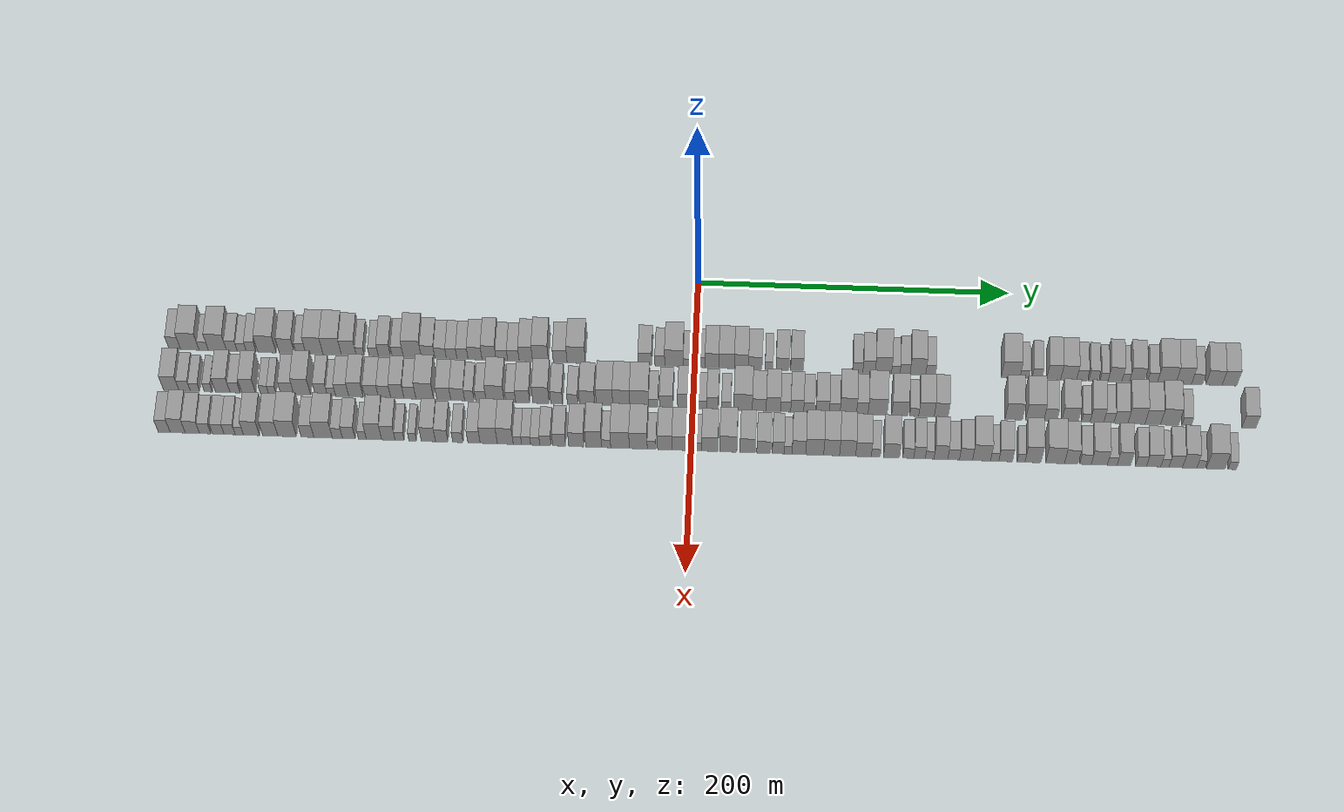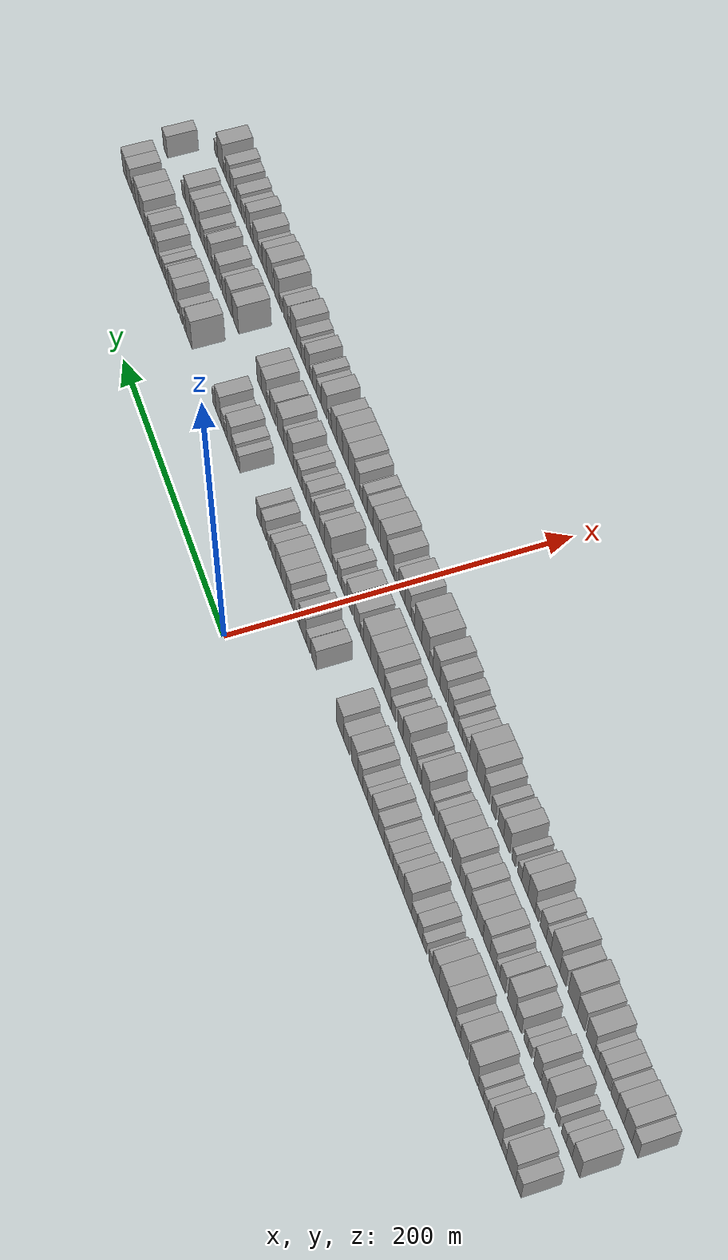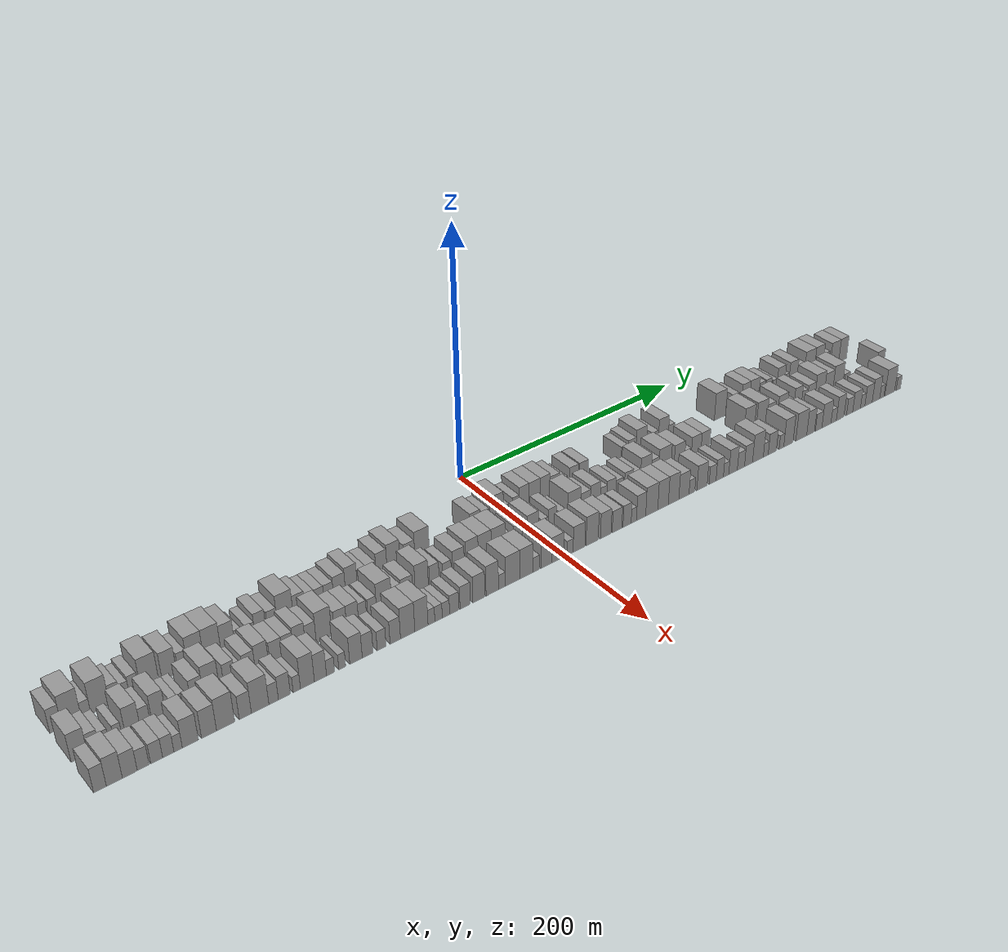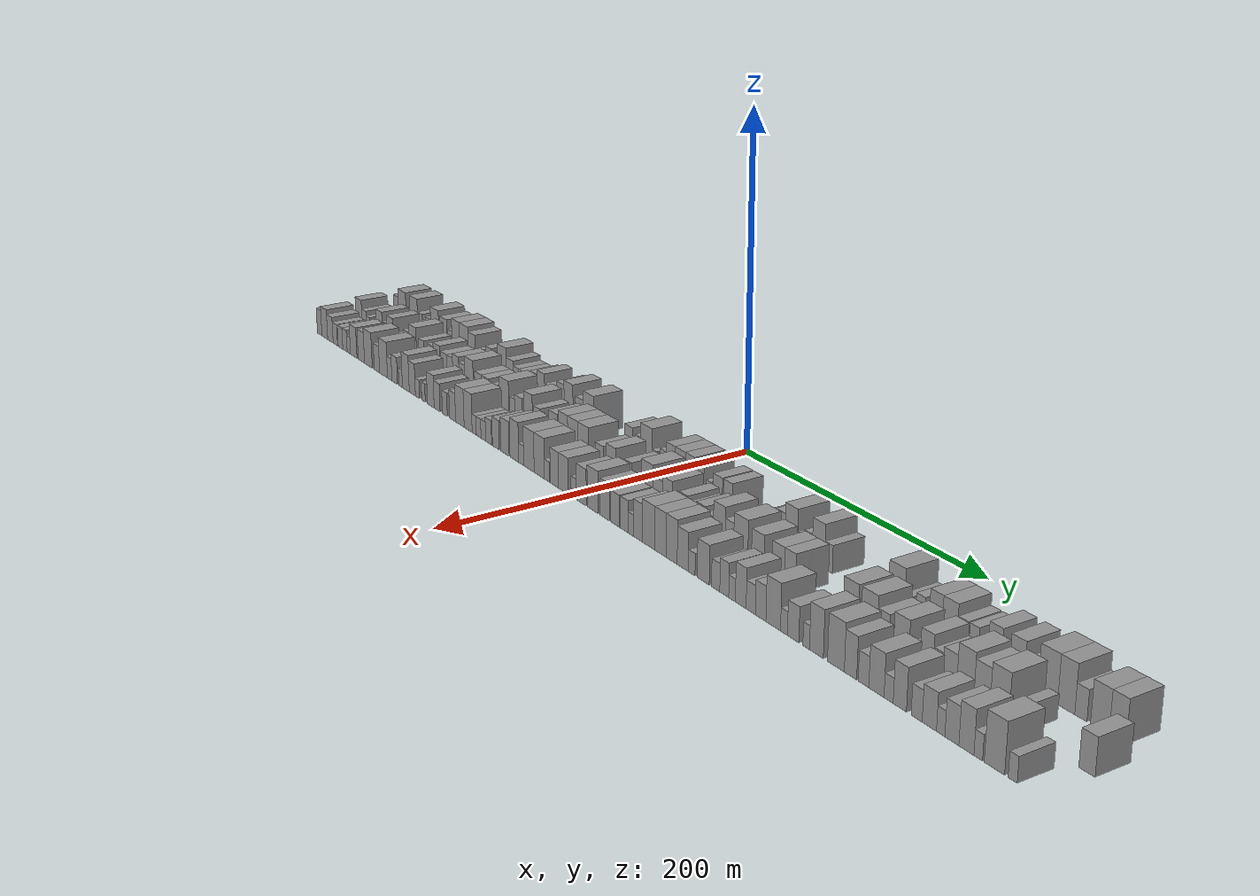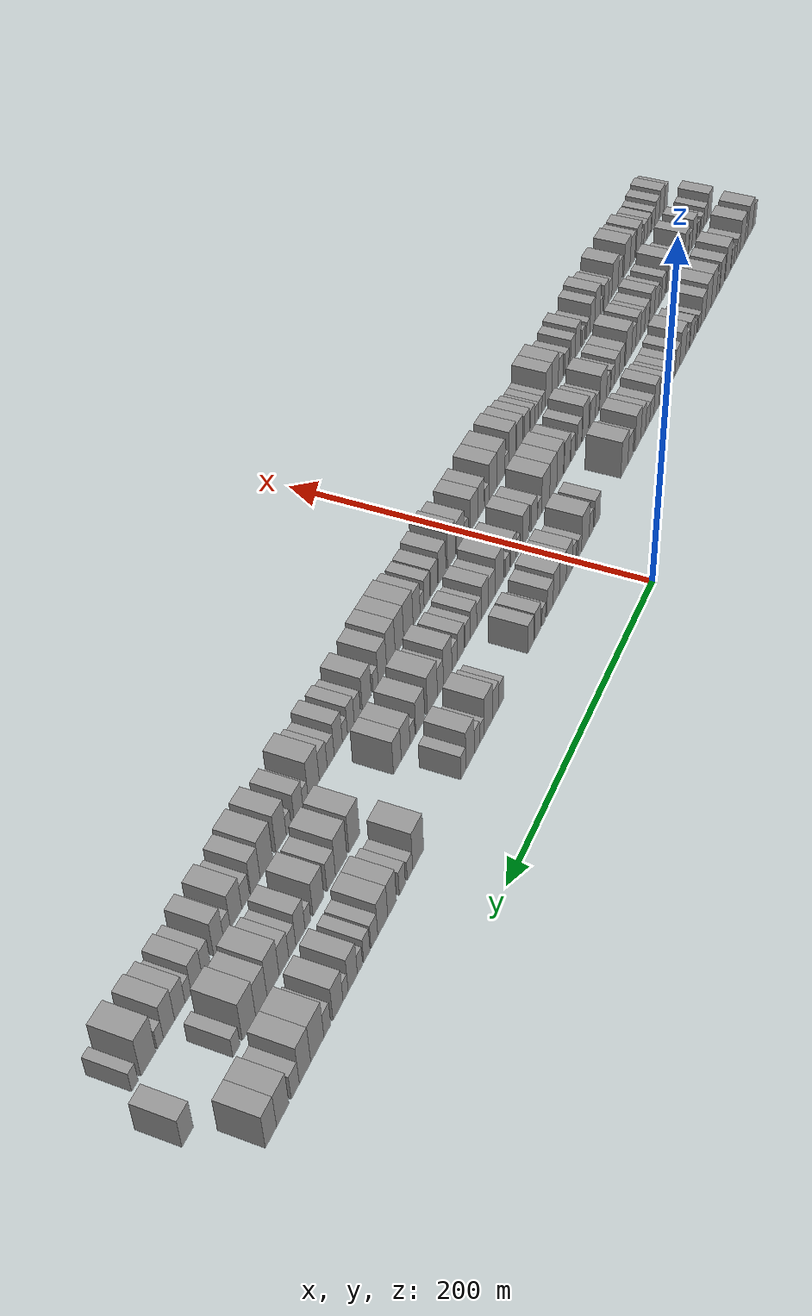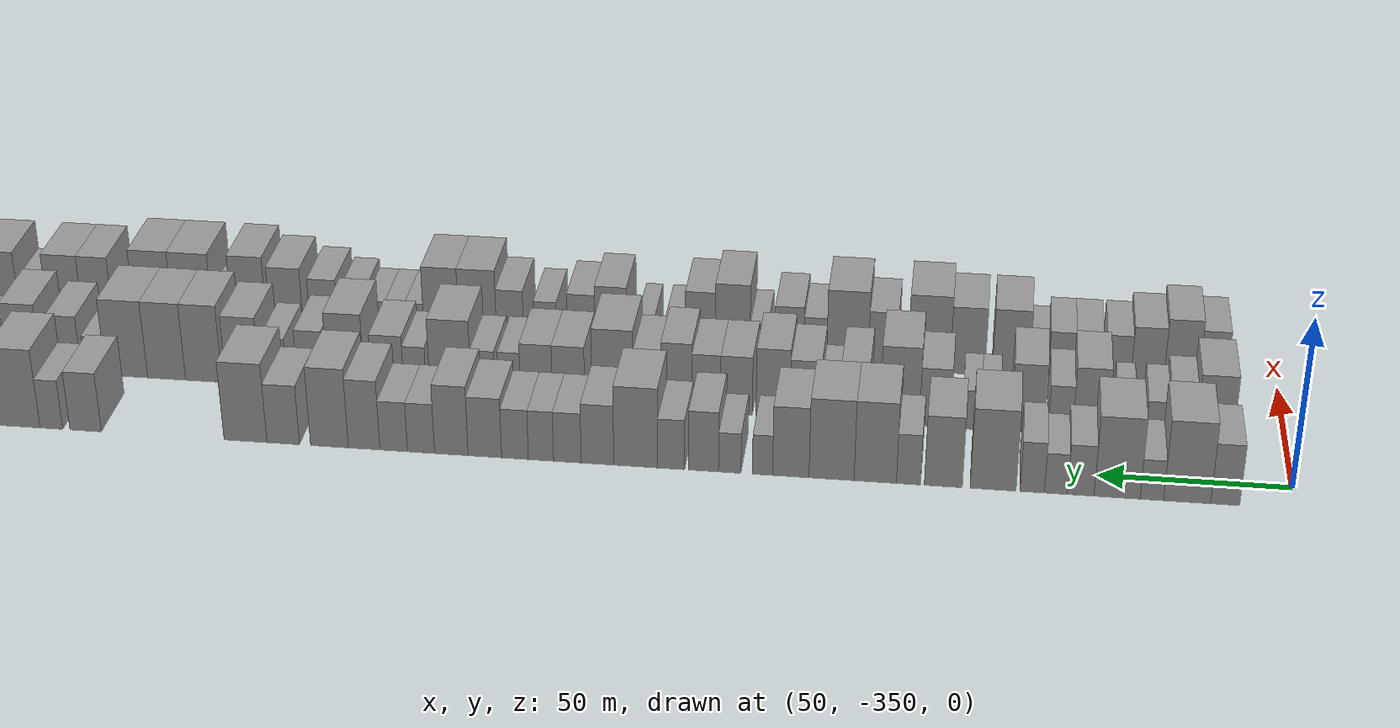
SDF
<sdf version="1.6">
 <world name="default">
  <scene>
   <sky><clouds><speed>12</speed></clouds></sky>
   <ambient>0.4 0.4 0.4 1</ambient>
   <background>0.7 0.7 0.7 1</background>
   <shadows>1</shadows>
  </scene>
  <gravity>0 0 -9.8066</gravity>
  <magnetic_field>6e-06 2.3e-05 -4.2e-05</magnetic_field>
  <physics default="0" name="default_physics" type="ode">
   <ode>
    <solver>
     <type>quick</type>
     <iters>10</iters>
     <sor>1.0</sor>
     <use_dynamic_moi_rescaling>0</use_dynamic_moi_rescaling>
    </solver>
    <constraints>
     <cfm>0</cfm>
     <erp>0.2</erp>
     <contact_max_correcting_vel>100</contact_max_correcting_vel>
     <contact_surface_layer>0.001</contact_surface_layer>
    </constraints>
   </ode>
   <max_step_size>0.004</max_step_size>
   <real_time_factor>1</real_time_factor>
   <real_time_update_rate>250</real_time_update_rate>
  </physics>
  <light name="sun" type="directional">
   <pose>0 0 10 0 0 0</pose>
   <diffuse>0.8 0.8 0.8 1</diffuse>
   <specular>0.2 0.2 0.2 1</specular>
   <attenuation>
    <range>1000</range>
    <constant>0.9</constant>
    <linear>0.01</linear>
    <quadratic>0.001</quadratic>
   </attenuation>
   <direction>-0.5 0.1 -0.9</direction>
  </light>
  <model name="building_1">
   <static>1</static>
   <pose>50.0000 -332.3108 0 0.000000 0.000000 0.000000</pose>
   <link name="link">
    <pose>0 0 9.00 0 0 0</pose>
    <collision name="collision"><geometry><box><size>20.0000 7.3784 18.0000</size></box></geometry></collision>
    <visual name="visual">
     <cast_shadows>0</cast_shadows>
     <geometry><box><size>20.0000 7.3784 18.0000</size></box></geometry>
     <material>
      <script>
       <uri>model://grey_wall/materials/scripts</uri>
       <uri>model://grey_wall/materials/textures</uri>
       <name>vrc/grey_wall</name>
      </script>
     </material>
    </visual>
   </link>
  </model>
  <model name="building_2">
   <static>1</static>
   <pose>50.0000 -322.6757 0 0.000000 0.000000 0.000000</pose>
   <link name="link">
    <pose>0 0 12.00 0 0 0</pose>
    <collision name="collision"><geometry><box><size>20.0000 11.8918 24.0000</size></box></geometry></collision>
    <visual name="visual">
     <cast_shadows>0</cast_shadows>
     <geometry><box><size>20.0000 11.8918 24.0000</size></box></geometry>
     <material>
      <script>
       <uri>model://grey_wall/materials/scripts</uri>
       <uri>model://grey_wall/materials/textures</uri>
       <name>vrc/grey_wall</name>
      </script>
     </material>
    </visual>
   </link>
  </model>
  <model name="building_3">
   <static>1</static>
   <pose>50.0000 -313.7521 0 0.000000 0.000000 0.000000</pose>
   <link name="link">
    <pose>0 0 6.00 0 0 0</pose>
    <collision name="collision"><geometry><box><size>20.0000 5.9555 12.0000</size></box></geometry></collision>
    <visual name="visual">
     <cast_shadows>0</cast_shadows>
     <geometry><box><size>20.0000 5.9555 12.0000</size></box></geometry>
     <material>
      <script>
       <uri>model://grey_wall/materials/scripts</uri>
       <uri>model://grey_wall/materials/textures</uri>
       <name>vrc/grey_wall</name>
      </script>
     </material>
    </visual>
   </link>
  </model>
  <model name="building_4">
   <static>1</static>
   <pose>50.0000 -304.9141 0 0.000000 0.000000 0.000000</pose>
   <link name="link">
    <pose>0 0 12.00 0 0 0</pose>
    <collision name="collision"><geometry><box><size>20.0000 11.7204 24.0000</size></box></geometry></collision>
    <visual name="visual">
     <cast_shadows>0</cast_shadows>
     <geometry><box><size>20.0000 11.7204 24.0000</size></box></geometry>
     <material>
      <script>
       <uri>model://grey_wall/materials/scripts</uri>
       <uri>model://grey_wall/materials/textures</uri>
       <name>vrc/grey_wall</name>
      </script>
     </material>
    </visual>
   </link>
  </model>
  <model name="building_5">
   <static>1</static>
   <pose>50.0000 -295.6579 0 0.000000 0.000000 0.000000</pose>
   <link name="link">
    <pose>0 0 7.50 0 0 0</pose>
    <collision name="collision"><geometry><box><size>20.0000 6.7922 15.0000</size></box></geometry></collision>
    <visual name="visual">
     <cast_shadows>0</cast_shadows>
     <geometry><box><size>20.0000 6.7922 15.0000</size></box></geometry>
     <material>
      <script>
       <uri>model://grey_wall/materials/scripts</uri>
       <uri>model://grey_wall/materials/textures</uri>
       <name>vrc/grey_wall</name>
      </script>
     </material>
    </visual>
   </link>
  </model>
  <model name="building_6">
   <static>1</static>
   <pose>50.0000 -289.3308 0 0.000000 0.000000 0.000000</pose>
   <link name="link">
    <pose>0 0 6.00 0 0 0</pose>
    <collision name="collision"><geometry><box><size>20.0000 5.8620 12.0000</size></box></geometry></collision>
    <visual name="visual">
     <cast_shadows>0</cast_shadows>
     <geometry><box><size>20.0000 5.8620 12.0000</size></box></geometry>
     <material>
      <script>
       <uri>model://grey_wall/materials/scripts</uri>
       <uri>model://grey_wall/materials/textures</uri>
       <name>vrc/grey_wall</name>
      </script>
     </material>
    </visual>
   </link>
  </model>
  <model name="building_7">
   <static>1</static>
   <pose>50.0000 -283.2751 0 0.000000 0.000000 0.000000</pose>
   <link name="link">
    <pose>0 0 7.50 0 0 0</pose>
    <collision name="collision"><geometry><box><size>20.0000 6.2495 15.0000</size></box></geometry></collision>
    <visual name="visual">
     <cast_shadows>0</cast_shadows>
     <geometry><box><size>20.0000 6.2495 15.0000</size></box></geometry>
     <material>
      <script>
       <uri>model://grey_wall/materials/scripts</uri>
       <uri>model://grey_wall/materials/textures</uri>
       <name>vrc/grey_wall</name>
      </script>
     </material>
    </visual>
   </link>
  </model>
  <model name="building_8">
   <static>1</static>
   <pose>50.0000 -273.2526 0 0.000000 0.000000 0.000000</pose>
   <link name="link">
    <pose>0 0 12.00 0 0 0</pose>
    <collision name="collision"><geometry><box><size>20.0000 11.7955 24.0000</size></box></geometry></collision>
    <visual name="visual">
     <cast_shadows>0</cast_shadows>
     <geometry><box><size>20.0000 11.7955 24.0000</size></box></geometry>
     <material>
      <script>
       <uri>model://grey_wall/materials/scripts</uri>
       <uri>model://grey_wall/materials/textures</uri>
       <name>vrc/grey_wall</name>
      </script>
     </material>
    </visual>
   </link>
  </model>
  <model name="building_9">
   <static>1</static>
   <pose>50.0000 -260.4622 0 0.000000 0.000000 0.000000</pose>
   <link name="link">
    <pose>0 0 10.50 0 0 0</pose>
    <collision name="collision"><geometry><box><size>20.0000 9.7853 21.0000</size></box></geometry></collision>
    <visual name="visual">
     <cast_shadows>0</cast_shadows>
     <geometry><box><size>20.0000 9.7853 21.0000</size></box></geometry>
     <material>
      <script>
       <uri>model://grey_wall/materials/scripts</uri>
       <uri>model://grey_wall/materials/textures</uri>
       <name>vrc/grey_wall</name>
      </script>
     </material>
    </visual>
   </link>
  </model>
  <model name="building_10">
   <static>1</static>
   <pose>50.0000 -251.4611 0 0.000000 0.000000 0.000000</pose>
   <link name="link">
    <pose>0 0 7.50 0 0 0</pose>
    <collision name="collision"><geometry><box><size>20.0000 6.2170 15.0000</size></box></geometry></collision>
    <visual name="visual">
     <cast_shadows>0</cast_shadows>
     <geometry><box><size>20.0000 6.2170 15.0000</size></box></geometry>
     <material>
      <script>
       <uri>model://grey_wall/materials/scripts</uri>
       <uri>model://grey_wall/materials/textures</uri>
       <name>vrc/grey_wall</name>
      </script>
     </material>
    </visual>
   </link>
  </model>
  <model name="building_11">
   <static>1</static>
   <pose>50.0000 -242.8656 0 0.000000 0.000000 0.000000</pose>
   <link name="link">
    <pose>0 0 12.00 0 0 0</pose>
    <collision name="collision"><geometry><box><size>20.0000 10.9740 24.0000</size></box></geometry></collision>
    <visual name="visual">
     <cast_shadows>0</cast_shadows>
     <geometry><box><size>20.0000 10.9740 24.0000</size></box></geometry>
     <material>
      <script>
       <uri>model://grey_wall/materials/scripts</uri>
       <uri>model://grey_wall/materials/textures</uri>
       <name>vrc/grey_wall</name>
      </script>
     </material>
    </visual>
   </link>
  </model>
  <model name="building_12">
   <static>1</static>
   <pose>50.0000 -231.5068 0 0.000000 0.000000 0.000000</pose>
   <link name="link">
    <pose>0 0 12.00 0 0 0</pose>
    <collision name="collision"><geometry><box><size>20.0000 11.7435 24.0000</size></box></geometry></collision>
    <visual name="visual">
     <cast_shadows>0</cast_shadows>
     <geometry><box><size>20.0000 11.7435 24.0000</size></box></geometry>
     <material>
      <script>
       <uri>model://grey_wall/materials/scripts</uri>
       <uri>model://grey_wall/materials/textures</uri>
       <name>vrc/grey_wall</name>
      </script>
     </material>
    </visual>
   </link>
  </model>
  <model name="building_13">
   <static>1</static>
   <pose>50.0000 -220.8834 0 0.000000 0.000000 0.000000</pose>
   <link name="link">
    <pose>0 0 10.50 0 0 0</pose>
    <collision name="collision"><geometry><box><size>20.0000 9.5034 21.0000</size></box></geometry></collision>
    <visual name="visual">
     <cast_shadows>0</cast_shadows>
     <geometry><box><size>20.0000 9.5034 21.0000</size></box></geometry>
     <material>
      <script>
       <uri>model://grey_wall/materials/scripts</uri>
       <uri>model://grey_wall/materials/textures</uri>
       <name>vrc/grey_wall</name>
      </script>
     </material>
    </visual>
   </link>
  </model>
  <model name="building_14">
   <static>1</static>
   <pose>50.0000 -213.5074 0 0.000000 0.000000 0.000000</pose>
   <link name="link">
    <pose>0 0 6.00 0 0 0</pose>
    <collision name="collision"><geometry><box><size>20.0000 5.2485 12.0000</size></box></geometry></collision>
    <visual name="visual">
     <cast_shadows>0</cast_shadows>
     <geometry><box><size>20.0000 5.2485 12.0000</size></box></geometry>
     <material>
      <script>
       <uri>model://grey_wall/materials/scripts</uri>
       <uri>model://grey_wall/materials/textures</uri>
       <name>vrc/grey_wall</name>
      </script>
     </material>
    </visual>
   </link>
  </model>
  <model name="building_15">
   <static>1</static>
   <pose>50.0000 -204.9327 0 0.000000 0.000000 0.000000</pose>
   <link name="link">
    <pose>0 0 6.00 0 0 0</pose>
    <collision name="collision"><geometry><box><size>20.0000 5.9009 12.0000</size></box></geometry></collision>
    <visual name="visual">
     <cast_shadows>0</cast_shadows>
     <geometry><box><size>20.0000 5.9009 12.0000</size></box></geometry>
     <material>
      <script>
       <uri>model://grey_wall/materials/scripts</uri>
       <uri>model://grey_wall/materials/textures</uri>
       <name>vrc/grey_wall</name>
      </script>
     </material>
    </visual>
   </link>
  </model>
  <model name="building_16">
   <static>1</static>
   <pose>50.0000 -198.0368 0 0.000000 0.000000 0.000000</pose>
   <link name="link">
    <pose>0 0 9.00 0 0 0</pose>
    <collision name="collision"><geometry><box><size>20.0000 7.8909 18.0000</size></box></geometry></collision>
    <visual name="visual">
     <cast_shadows>0</cast_shadows>
     <geometry><box><size>20.0000 7.8909 18.0000</size></box></geometry>
     <material>
      <script>
       <uri>model://grey_wall/materials/scripts</uri>
       <uri>model://grey_wall/materials/textures</uri>
       <name>vrc/grey_wall</name>
      </script>
     </material>
    </visual>
   </link>
  </model>
  <model name="building_17">
   <static>1</static>
   <pose>50.0000 -189.5575 0 0.000000 0.000000 0.000000</pose>
   <link name="link">
    <pose>0 0 7.50 0 0 0</pose>
    <collision name="collision"><geometry><box><size>20.0000 7.0677 15.0000</size></box></geometry></collision>
    <visual name="visual">
     <cast_shadows>0</cast_shadows>
     <geometry><box><size>20.0000 7.0677 15.0000</size></box></geometry>
     <material>
      <script>
       <uri>model://grey_wall/materials/scripts</uri>
       <uri>model://grey_wall/materials/textures</uri>
       <name>vrc/grey_wall</name>
      </script>
     </material>
    </visual>
   </link>
  </model>
  <model name="building_18">
   <static>1</static>
   <pose>50.0000 -180.2230 0 0.000000 0.000000 0.000000</pose>
   <link name="link">
    <pose>0 0 12.00 0 0 0</pose>
    <collision name="collision"><geometry><box><size>20.0000 11.6012 24.0000</size></box></geometry></collision>
    <visual name="visual">
     <cast_shadows>0</cast_shadows>
     <geometry><box><size>20.0000 11.6012 24.0000</size></box></geometry>
     <material>
      <script>
       <uri>model://grey_wall/materials/scripts</uri>
       <uri>model://grey_wall/materials/textures</uri>
       <name>vrc/grey_wall</name>
      </script>
     </material>
    </visual>
   </link>
  </model>
  <model name="building_19">
   <static>1</static>
   <pose>50.0000 -170.1049 0 0.000000 0.000000 0.000000</pose>
   <link name="link">
    <pose>0 0 9.00 0 0 0</pose>
    <collision name="collision"><geometry><box><size>20.0000 8.6351 18.0000</size></box></geometry></collision>
    <visual name="visual">
     <cast_shadows>0</cast_shadows>
     <geometry><box><size>20.0000 8.6351 18.0000</size></box></geometry>
     <material>
      <script>
       <uri>model://grey_wall/materials/scripts</uri>
       <uri>model://grey_wall/materials/textures</uri>
       <name>vrc/grey_wall</name>
      </script>
     </material>
    </visual>
   </link>
  </model>
  <model name="building_20">
   <static>1</static>
   <pose>50.0000 -162.1165 0 0.000000 0.000000 0.000000</pose>
   <link name="link">
    <pose>0 0 7.50 0 0 0</pose>
    <collision name="collision"><geometry><box><size>20.0000 7.3418 15.0000</size></box></geometry></collision>
    <visual name="visual">
     <cast_shadows>0</cast_shadows>
     <geometry><box><size>20.0000 7.3418 15.0000</size></box></geometry>
     <material>
      <script>
       <uri>model://grey_wall/materials/scripts</uri>
       <uri>model://grey_wall/materials/textures</uri>
       <name>vrc/grey_wall</name>
      </script>
     </material>
    </visual>
   </link>
  </model>
  <model name="building_21">
   <static>1</static>
   <pose>50.0000 -155.0835 0 0.000000 0.000000 0.000000</pose>
   <link name="link">
    <pose>0 0 7.50 0 0 0</pose>
    <collision name="collision"><geometry><box><size>20.0000 6.7240 15.0000</size></box></geometry></collision>
    <visual name="visual">
     <cast_shadows>0</cast_shadows>
     <geometry><box><size>20.0000 6.7240 15.0000</size></box></geometry>
     <material>
      <script>
       <uri>model://grey_wall/materials/scripts</uri>
       <uri>model://grey_wall/materials/textures</uri>
       <name>vrc/grey_wall</name>
      </script>
     </material>
    </visual>
   </link>
  </model>
  <model name="building_22">
   <static>1</static>
   <pose>50.0000 -148.1666 0 0.000000 0.000000 0.000000</pose>
   <link name="link">
    <pose>0 0 7.50 0 0 0</pose>
    <collision name="collision"><geometry><box><size>20.0000 7.1098 15.0000</size></box></geometry></collision>
    <visual name="visual">
     <cast_shadows>0</cast_shadows>
     <geometry><box><size>20.0000 7.1098 15.0000</size></box></geometry>
     <material>
      <script>
       <uri>model://grey_wall/materials/scripts</uri>
       <uri>model://grey_wall/materials/textures</uri>
       <name>vrc/grey_wall</name>
      </script>
     </material>
    </visual>
   </link>
  </model>
  <model name="building_23">
   <static>1</static>
   <pose>50.0000 -140.1274 0 0.000000 0.000000 0.000000</pose>
   <link name="link">
    <pose>0 0 9.00 0 0 0</pose>
    <collision name="collision"><geometry><box><size>20.0000 8.9688 18.0000</size></box></geometry></collision>
    <visual name="visual">
     <cast_shadows>0</cast_shadows>
     <geometry><box><size>20.0000 8.9688 18.0000</size></box></geometry>
     <material>
      <script>
       <uri>model://grey_wall/materials/scripts</uri>
       <uri>model://grey_wall/materials/textures</uri>
       <name>vrc/grey_wall</name>
      </script>
     </material>
    </visual>
   </link>
  </model>
  <model name="building_24">
   <static>1</static>
   <pose>50.0000 -131.1385 0 0.000000 0.000000 0.000000</pose>
   <link name="link">
    <pose>0 0 10.50 0 0 0</pose>
    <collision name="collision"><geometry><box><size>20.0000 9.0091 21.0000</size></box></geometry></collision>
    <visual name="visual">
     <cast_shadows>0</cast_shadows>
     <geometry><box><size>20.0000 9.0091 21.0000</size></box></geometry>
     <material>
      <script>
       <uri>model://grey_wall/materials/scripts</uri>
       <uri>model://grey_wall/materials/textures</uri>
       <name>vrc/grey_wall</name>
      </script>
     </material>
    </visual>
   </link>
  </model>
  <model name="building_25">
   <static>1</static>
   <pose>50.0000 -122.9975 0 0.000000 0.000000 0.000000</pose>
   <link name="link">
    <pose>0 0 7.50 0 0 0</pose>
    <collision name="collision"><geometry><box><size>20.0000 7.2728 15.0000</size></box></geometry></collision>
    <visual name="visual">
     <cast_shadows>0</cast_shadows>
     <geometry><box><size>20.0000 7.2728 15.0000</size></box></geometry>
     <material>
      <script>
       <uri>model://grey_wall/materials/scripts</uri>
       <uri>model://grey_wall/materials/textures</uri>
       <name>vrc/grey_wall</name>
      </script>
     </material>
    </visual>
   </link>
  </model>
  <model name="building_26">
   <static>1</static>
   <pose>50.0000 -115.6475 0 0.000000 0.000000 0.000000</pose>
   <link name="link">
    <pose>0 0 7.50 0 0 0</pose>
    <collision name="collision"><geometry><box><size>20.0000 7.4273 15.0000</size></box></geometry></collision>
    <visual name="visual">
     <cast_shadows>0</cast_shadows>
     <geometry><box><size>20.0000 7.4273 15.0000</size></box></geometry>
     <material>
      <script>
       <uri>model://grey_wall/materials/scripts</uri>
       <uri>model://grey_wall/materials/textures</uri>
       <name>vrc/grey_wall</name>
      </script>
     </material>
    </visual>
   </link>
  </model>
  <model name="building_27">
   <static>1</static>
   <pose>50.0000 -107.6770 0 0.000000 0.000000 0.000000</pose>
   <link name="link">
    <pose>0 0 10.50 0 0 0</pose>
    <collision name="collision"><geometry><box><size>20.0000 8.5136 21.0000</size></box></geometry></collision>
    <visual name="visual">
     <cast_shadows>0</cast_shadows>
     <geometry><box><size>20.0000 8.5136 21.0000</size></box></geometry>
     <material>
      <script>
       <uri>model://grey_wall/materials/scripts</uri>
       <uri>model://grey_wall/materials/textures</uri>
       <name>vrc/grey_wall</name>
      </script>
     </material>
    </visual>
   </link>
  </model>
  <model name="building_28">
   <static>1</static>
   <pose>50.0000 -98.3052 0 0.000000 0.000000 0.000000</pose>
   <link name="link">
    <pose>0 0 12.00 0 0 0</pose>
    <collision name="collision"><geometry><box><size>20.0000 10.2300 24.0000</size></box></geometry></collision>
    <visual name="visual">
     <cast_shadows>0</cast_shadows>
     <geometry><box><size>20.0000 10.2300 24.0000</size></box></geometry>
     <material>
      <script>
       <uri>model://grey_wall/materials/scripts</uri>
       <uri>model://grey_wall/materials/textures</uri>
       <name>vrc/grey_wall</name>
      </script>
     </material>
    </visual>
   </link>
  </model>
  <model name="building_29">
   <static>1</static>
   <pose>50.0000 -85.7666 0 0.000000 0.000000 0.000000</pose>
   <link name="link">
    <pose>0 0 9.00 0 0 0</pose>
    <collision name="collision"><geometry><box><size>20.0000 8.8471 18.0000</size></box></geometry></collision>
    <visual name="visual">
     <cast_shadows>0</cast_shadows>
     <geometry><box><size>20.0000 8.8471 18.0000</size></box></geometry>
     <material>
      <script>
       <uri>model://grey_wall/materials/scripts</uri>
       <uri>model://grey_wall/materials/textures</uri>
       <name>vrc/grey_wall</name>
      </script>
     </material>
    </visual>
   </link>
  </model>
  <model name="building_30">
   <static>1</static>
   <pose>50.0000 -75.5026 0 0.000000 0.000000 0.000000</pose>
   <link name="link">
    <pose>0 0 12.00 0 0 0</pose>
    <collision name="collision"><geometry><box><size>20.0000 11.6808 24.0000</size></box></geometry></collision>
    <visual name="visual">
     <cast_shadows>0</cast_shadows>
     <geometry><box><size>20.0000 11.6808 24.0000</size></box></geometry>
     <material>
      <script>
       <uri>model://grey_wall/materials/scripts</uri>
       <uri>model://grey_wall/materials/textures</uri>
       <name>vrc/grey_wall</name>
      </script>
     </material>
    </visual>
   </link>
  </model>
  <model name="building_31">
   <static>1</static>
   <pose>50.0000 -31.6511 0 0.000000 0.000000 0.000000</pose>
   <link name="link">
    <pose>0 0 9.00 0 0 0</pose>
    <collision name="collision"><geometry><box><size>20.0000 8.6741 18.0000</size></box></geometry></collision>
    <visual name="visual">
     <cast_shadows>0</cast_shadows>
     <geometry><box><size>20.0000 8.6741 18.0000</size></box></geometry>
     <material>
      <script>
       <uri>model://grey_wall/materials/scripts</uri>
       <uri>model://grey_wall/materials/textures</uri>
       <name>vrc/grey_wall</name>
      </script>
     </material>
    </visual>
   </link>
  </model>
  <model name="building_32">
   <static>1</static>
   <pose>50.0000 -22.1892 0 0.000000 0.000000 0.000000</pose>
   <link name="link">
    <pose>0 0 7.50 0 0 0</pose>
    <collision name="collision"><geometry><box><size>20.0000 6.2497 15.0000</size></box></geometry></collision>
    <visual name="visual">
     <cast_shadows>0</cast_shadows>
     <geometry><box><size>20.0000 6.2497 15.0000</size></box></geometry>
     <material>
      <script>
       <uri>model://grey_wall/materials/scripts</uri>
       <uri>model://grey_wall/materials/textures</uri>
       <name>vrc/grey_wall</name>
      </script>
     </material>
    </visual>
   </link>
  </model>
  <model name="building_33">
   <static>1</static>
   <pose>50.0000 -13.2062 0 0.000000 0.000000 0.000000</pose>
   <link name="link">
    <pose>0 0 12.00 0 0 0</pose>
    <collision name="collision"><geometry><box><size>20.0000 11.7163 24.0000</size></box></geometry></collision>
    <visual name="visual">
     <cast_shadows>0</cast_shadows>
     <geometry><box><size>20.0000 11.7163 24.0000</size></box></geometry>
     <material>
      <script>
       <uri>model://grey_wall/materials/scripts</uri>
       <uri>model://grey_wall/materials/textures</uri>
       <name>vrc/grey_wall</name>
      </script>
     </material>
    </visual>
   </link>
  </model>
  <model name="building_34">
   <static>1</static>
   <pose>50.0000 -4.9149 0 0.000000 0.000000 0.000000</pose>
   <link name="link">
    <pose>0 0 6.00 0 0 0</pose>
    <collision name="collision"><geometry><box><size>20.0000 4.8664 12.0000</size></box></geometry></collision>
    <visual name="visual">
     <cast_shadows>0</cast_shadows>
     <geometry><box><size>20.0000 4.8664 12.0000</size></box></geometry>
     <material>
      <script>
       <uri>model://grey_wall/materials/scripts</uri>
       <uri>model://grey_wall/materials/textures</uri>
       <name>vrc/grey_wall</name>
      </script>
     </material>
    </visual>
   </link>
  </model>
  <model name="building_35">
   <static>1</static>
   <pose>50.0000 3.5625 0 0.000000 0.000000 0.000000</pose>
   <link name="link">
    <pose>0 0 7.50 0 0 0</pose>
    <collision name="collision"><geometry><box><size>20.0000 6.0884 15.0000</size></box></geometry></collision>
    <visual name="visual">
     <cast_shadows>0</cast_shadows>
     <geometry><box><size>20.0000 6.0884 15.0000</size></box></geometry>
     <material>
      <script>
       <uri>model://grey_wall/materials/scripts</uri>
       <uri>model://grey_wall/materials/textures</uri>
       <name>vrc/grey_wall</name>
      </script>
     </material>
    </visual>
   </link>
  </model>
  <model name="building_36">
   <static>1</static>
   <pose>50.0000 10.9737 0 0.000000 0.000000 0.000000</pose>
   <link name="link">
    <pose>0 0 10.50 0 0 0</pose>
    <collision name="collision"><geometry><box><size>20.0000 8.7339 21.0000</size></box></geometry></collision>
    <visual name="visual">
     <cast_shadows>0</cast_shadows>
     <geometry><box><size>20.0000 8.7339 21.0000</size></box></geometry>
     <material>
      <script>
       <uri>model://grey_wall/materials/scripts</uri>
       <uri>model://grey_wall/materials/textures</uri>
       <name>vrc/grey_wall</name>
      </script>
     </material>
    </visual>
   </link>
  </model>
  <model name="building_37">
   <static>1</static>
   <pose>50.0000 20.2652 0 0.000000 0.000000 0.000000</pose>
   <link name="link">
    <pose>0 0 10.50 0 0 0</pose>
    <collision name="collision"><geometry><box><size>20.0000 9.8492 21.0000</size></box></geometry></collision>
    <visual name="visual">
     <cast_shadows>0</cast_shadows>
     <geometry><box><size>20.0000 9.8492 21.0000</size></box></geometry>
     <material>
      <script>
       <uri>model://grey_wall/materials/scripts</uri>
       <uri>model://grey_wall/materials/textures</uri>
       <name>vrc/grey_wall</name>
      </script>
     </material>
    </visual>
   </link>
  </model>
  <model name="building_38">
   <static>1</static>
   <pose>50.0000 29.7162 0 0.000000 0.000000 0.000000</pose>
   <link name="link">
    <pose>0 0 10.50 0 0 0</pose>
    <collision name="collision"><geometry><box><size>20.0000 9.0526 21.0000</size></box></geometry></collision>
    <visual name="visual">
     <cast_shadows>0</cast_shadows>
     <geometry><box><size>20.0000 9.0526 21.0000</size></box></geometry>
     <material>
      <script>
       <uri>model://grey_wall/materials/scripts</uri>
       <uri>model://grey_wall/materials/textures</uri>
       <name>vrc/grey_wall</name>
      </script>
     </material>
    </visual>
   </link>
  </model>
  <model name="building_39">
   <static>1</static>
   <pose>50.0000 38.5405 0 0.000000 0.000000 0.000000</pose>
   <link name="link">
    <pose>0 0 9.00 0 0 0</pose>
    <collision name="collision"><geometry><box><size>20.0000 8.5960 18.0000</size></box></geometry></collision>
    <visual name="visual">
     <cast_shadows>0</cast_shadows>
     <geometry><box><size>20.0000 8.5960 18.0000</size></box></geometry>
     <material>
      <script>
       <uri>model://grey_wall/materials/scripts</uri>
       <uri>model://grey_wall/materials/textures</uri>
       <name>vrc/grey_wall</name>
      </script>
     </material>
    </visual>
   </link>
  </model>
  <model name="building_40">
   <static>1</static>
   <pose>50.0000 47.3137 0 0.000000 0.000000 0.000000</pose>
   <link name="link">
    <pose>0 0 6.00 0 0 0</pose>
    <collision name="collision"><geometry><box><size>20.0000 4.9505 12.0000</size></box></geometry></collision>
    <visual name="visual">
     <cast_shadows>0</cast_shadows>
     <geometry><box><size>20.0000 4.9505 12.0000</size></box></geometry>
     <material>
      <script>
       <uri>model://grey_wall/materials/scripts</uri>
       <uri>model://grey_wall/materials/textures</uri>
       <name>vrc/grey_wall</name>
      </script>
     </material>
    </visual>
   </link>
  </model>
  <model name="building_41">
   <static>1</static>
   <pose>50.0000 55.9212 0 0.000000 0.000000 0.000000</pose>
   <link name="link">
    <pose>0 0 9.00 0 0 0</pose>
    <collision name="collision"><geometry><box><size>20.0000 8.2644 18.0000</size></box></geometry></collision>
    <visual name="visual">
     <cast_shadows>0</cast_shadows>
     <geometry><box><size>20.0000 8.2644 18.0000</size></box></geometry>
     <material>
      <script>
       <uri>model://grey_wall/materials/scripts</uri>
       <uri>model://grey_wall/materials/textures</uri>
       <name>vrc/grey_wall</name>
      </script>
     </material>
    </visual>
   </link>
  </model>
  <model name="building_42">
   <static>1</static>
   <pose>50.0000 65.1122 0 0.000000 0.000000 0.000000</pose>
   <link name="link">
    <pose>0 0 9.00 0 0 0</pose>
    <collision name="collision"><geometry><box><size>20.0000 8.1175 18.0000</size></box></geometry></collision>
    <visual name="visual">
     <cast_shadows>0</cast_shadows>
     <geometry><box><size>20.0000 8.1175 18.0000</size></box></geometry>
     <material>
      <script>
       <uri>model://grey_wall/materials/scripts</uri>
       <uri>model://grey_wall/materials/textures</uri>
       <name>vrc/grey_wall</name>
      </script>
     </material>
    </visual>
   </link>
  </model>
  <model name="building_43">
   <static>1</static>
   <pose>50.0000 103.7568 0 0.000000 0.000000 0.000000</pose>
   <link name="link">
    <pose>0 0 7.50 0 0 0</pose>
    <collision name="collision"><geometry><box><size>20.0000 6.3906 15.0000</size></box></geometry></collision>
    <visual name="visual">
     <cast_shadows>0</cast_shadows>
     <geometry><box><size>20.0000 6.3906 15.0000</size></box></geometry>
     <material>
      <script>
       <uri>model://grey_wall/materials/scripts</uri>
       <uri>model://grey_wall/materials/textures</uri>
       <name>vrc/grey_wall</name>
      </script>
     </material>
    </visual>
   </link>
  </model>
  <model name="building_44">
   <static>1</static>
   <pose>50.0000 110.8456 0 0.000000 0.000000 0.000000</pose>
   <link name="link">
    <pose>0 0 9.00 0 0 0</pose>
    <collision name="collision"><geometry><box><size>20.0000 7.7872 18.0000</size></box></geometry></collision>
    <visual name="visual">
     <cast_shadows>0</cast_shadows>
     <geometry><box><size>20.0000 7.7872 18.0000</size></box></geometry>
     <material>
      <script>
       <uri>model://grey_wall/materials/scripts</uri>
       <uri>model://grey_wall/materials/textures</uri>
       <name>vrc/grey_wall</name>
      </script>
     </material>
    </visual>
   </link>
  </model>
  <model name="building_45">
   <static>1</static>
   <pose>50.0000 119.9501 0 0.000000 0.000000 0.000000</pose>
   <link name="link">
    <pose>0 0 12.00 0 0 0</pose>
    <collision name="collision"><geometry><box><size>20.0000 10.4216 24.0000</size></box></geometry></collision>
    <visual name="visual">
     <cast_shadows>0</cast_shadows>
     <geometry><box><size>20.0000 10.4216 24.0000</size></box></geometry>
     <material>
      <script>
       <uri>model://grey_wall/materials/scripts</uri>
       <uri>model://grey_wall/materials/textures</uri>
       <name>vrc/grey_wall</name>
      </script>
     </material>
    </visual>
   </link>
  </model>
  <model name="building_46">
   <static>1</static>
   <pose>50.0000 127.8922 0 0.000000 0.000000 0.000000</pose>
   <link name="link">
    <pose>0 0 6.00 0 0 0</pose>
    <collision name="collision"><geometry><box><size>20.0000 5.4625 12.0000</size></box></geometry></collision>
    <visual name="visual">
     <cast_shadows>0</cast_shadows>
     <geometry><box><size>20.0000 5.4625 12.0000</size></box></geometry>
     <material>
      <script>
       <uri>model://grey_wall/materials/scripts</uri>
       <uri>model://grey_wall/materials/textures</uri>
       <name>vrc/grey_wall</name>
      </script>
     </material>
    </visual>
   </link>
  </model>
  <model name="building_47">
   <static>1</static>
   <pose>50.0000 133.8123 0 0.000000 0.000000 0.000000</pose>
   <link name="link">
    <pose>0 0 7.50 0 0 0</pose>
    <collision name="collision"><geometry><box><size>20.0000 6.3777 15.0000</size></box></geometry></collision>
    <visual name="visual">
     <cast_shadows>0</cast_shadows>
     <geometry><box><size>20.0000 6.3777 15.0000</size></box></geometry>
     <material>
      <script>
       <uri>model://grey_wall/materials/scripts</uri>
       <uri>model://grey_wall/materials/textures</uri>
       <name>vrc/grey_wall</name>
      </script>
     </material>
    </visual>
   </link>
  </model>
  <model name="building_48">
   <static>1</static>
   <pose>50.0000 141.9819 0 0.000000 0.000000 0.000000</pose>
   <link name="link">
    <pose>0 0 12.00 0 0 0</pose>
    <collision name="collision"><geometry><box><size>20.0000 9.9615 24.0000</size></box></geometry></collision>
    <visual name="visual">
     <cast_shadows>0</cast_shadows>
     <geometry><box><size>20.0000 9.9615 24.0000</size></box></geometry>
     <material>
      <script>
       <uri>model://grey_wall/materials/scripts</uri>
       <uri>model://grey_wall/materials/textures</uri>
       <name>vrc/grey_wall</name>
      </script>
     </material>
    </visual>
   </link>
  </model>
  <model name="building_49">
   <static>1</static>
   <pose>50.0000 150.0803 0 0.000000 0.000000 0.000000</pose>
   <link name="link">
    <pose>0 0 7.50 0 0 0</pose>
    <collision name="collision"><geometry><box><size>20.0000 6.2354 15.0000</size></box></geometry></collision>
    <visual name="visual">
     <cast_shadows>0</cast_shadows>
     <geometry><box><size>20.0000 6.2354 15.0000</size></box></geometry>
     <material>
      <script>
       <uri>model://grey_wall/materials/scripts</uri>
       <uri>model://grey_wall/materials/textures</uri>
       <name>vrc/grey_wall</name>
      </script>
     </material>
    </visual>
   </link>
  </model>
  <model name="building_50">
   <static>1</static>
   <pose>50.0000 200.9176 0 0.000000 0.000000 0.000000</pose>
   <link name="link">
    <pose>0 0 12.00 0 0 0</pose>
    <collision name="collision"><geometry><box><size>20.0000 11.8130 24.0000</size></box></geometry></collision>
    <visual name="visual">
     <cast_shadows>0</cast_shadows>
     <geometry><box><size>20.0000 11.8130 24.0000</size></box></geometry>
     <material>
      <script>
       <uri>model://grey_wall/materials/scripts</uri>
       <uri>model://grey_wall/materials/textures</uri>
       <name>vrc/grey_wall</name>
      </script>
     </material>
    </visual>
   </link>
  </model>
  <model name="building_51">
   <static>1</static>
   <pose>50.0000 209.6882 0 0.000000 0.000000 0.000000</pose>
   <link name="link">
    <pose>0 0 6.00 0 0 0</pose>
    <collision name="collision"><geometry><box><size>20.0000 5.7282 12.0000</size></box></geometry></collision>
    <visual name="visual">
     <cast_shadows>0</cast_shadows>
     <geometry><box><size>20.0000 5.7282 12.0000</size></box></geometry>
     <material>
      <script>
       <uri>model://grey_wall/materials/scripts</uri>
       <uri>model://grey_wall/materials/textures</uri>
       <name>vrc/grey_wall</name>
      </script>
     </material>
    </visual>
   </link>
  </model>
  <model name="building_52">
   <static>1</static>
   <pose>50.0000 217.7186 0 0.000000 0.000000 0.000000</pose>
   <link name="link">
    <pose>0 0 7.50 0 0 0</pose>
    <collision name="collision"><geometry><box><size>20.0000 6.3327 15.0000</size></box></geometry></collision>
    <visual name="visual">
     <cast_shadows>0</cast_shadows>
     <geometry><box><size>20.0000 6.3327 15.0000</size></box></geometry>
     <material>
      <script>
       <uri>model://grey_wall/materials/scripts</uri>
       <uri>model://grey_wall/materials/textures</uri>
       <name>vrc/grey_wall</name>
      </script>
     </material>
    </visual>
   </link>
  </model>
  <model name="building_53">
   <static>1</static>
   <pose>50.0000 228.3293 0 0.000000 0.000000 0.000000</pose>
   <link name="link">
    <pose>0 0 10.50 0 0 0</pose>
    <collision name="collision"><geometry><box><size>20.0000 8.8886 21.0000</size></box></geometry></collision>
    <visual name="visual">
     <cast_shadows>0</cast_shadows>
     <geometry><box><size>20.0000 8.8886 21.0000</size></box></geometry>
     <material>
      <script>
       <uri>model://grey_wall/materials/scripts</uri>
       <uri>model://grey_wall/materials/textures</uri>
       <name>vrc/grey_wall</name>
      </script>
     </material>
    </visual>
   </link>
  </model>
  <model name="building_54">
   <static>1</static>
   <pose>50.0000 237.7962 0 0.000000 0.000000 0.000000</pose>
   <link name="link">
    <pose>0 0 10.50 0 0 0</pose>
    <collision name="collision"><geometry><box><size>20.0000 10.0452 21.0000</size></box></geometry></collision>
    <visual name="visual">
     <cast_shadows>0</cast_shadows>
     <geometry><box><size>20.0000 10.0452 21.0000</size></box></geometry>
     <material>
      <script>
       <uri>model://grey_wall/materials/scripts</uri>
       <uri>model://grey_wall/materials/textures</uri>
       <name>vrc/grey_wall</name>
      </script>
     </material>
    </visual>
   </link>
  </model>
  <model name="building_55">
   <static>1</static>
   <pose>50.0000 246.1873 0 0.000000 0.000000 0.000000</pose>
   <link name="link">
    <pose>0 0 7.50 0 0 0</pose>
    <collision name="collision"><geometry><box><size>20.0000 6.7370 15.0000</size></box></geometry></collision>
    <visual name="visual">
     <cast_shadows>0</cast_shadows>
     <geometry><box><size>20.0000 6.7370 15.0000</size></box></geometry>
     <material>
      <script>
       <uri>model://grey_wall/materials/scripts</uri>
       <uri>model://grey_wall/materials/textures</uri>
       <name>vrc/grey_wall</name>
      </script>
     </material>
    </visual>
   </link>
  </model>
  <model name="building_56">
   <static>1</static>
   <pose>50.0000 253.6301 0 0.000000 0.000000 0.000000</pose>
   <link name="link">
    <pose>0 0 7.50 0 0 0</pose>
    <collision name="collision"><geometry><box><size>20.0000 6.1486 15.0000</size></box></geometry></collision>
    <visual name="visual">
     <cast_shadows>0</cast_shadows>
     <geometry><box><size>20.0000 6.1486 15.0000</size></box></geometry>
     <material>
      <script>
       <uri>model://grey_wall/materials/scripts</uri>
       <uri>model://grey_wall/materials/textures</uri>
       <name>vrc/grey_wall</name>
      </script>
     </material>
    </visual>
   </link>
  </model>
  <model name="building_57">
   <static>1</static>
   <pose>50.0000 260.2373 0 0.000000 0.000000 0.000000</pose>
   <link name="link">
    <pose>0 0 6.00 0 0 0</pose>
    <collision name="collision"><geometry><box><size>20.0000 5.0658 12.0000</size></box></geometry></collision>
    <visual name="visual">
     <cast_shadows>0</cast_shadows>
     <geometry><box><size>20.0000 5.0658 12.0000</size></box></geometry>
     <material>
      <script>
       <uri>model://grey_wall/materials/scripts</uri>
       <uri>model://grey_wall/materials/textures</uri>
       <name>vrc/grey_wall</name>
      </script>
     </material>
    </visual>
   </link>
  </model>
  <model name="building_58">
   <static>1</static>
   <pose>50.0000 267.1651 0 0.000000 0.000000 0.000000</pose>
   <link name="link">
    <pose>0 0 10.50 0 0 0</pose>
    <collision name="collision"><geometry><box><size>20.0000 8.7898 21.0000</size></box></geometry></collision>
    <visual name="visual">
     <cast_shadows>0</cast_shadows>
     <geometry><box><size>20.0000 8.7898 21.0000</size></box></geometry>
     <material>
      <script>
       <uri>model://grey_wall/materials/scripts</uri>
       <uri>model://grey_wall/materials/textures</uri>
       <name>vrc/grey_wall</name>
      </script>
     </material>
    </visual>
   </link>
  </model>
  <model name="building_59">
   <static>1</static>
   <pose>50.0000 273.9715 0 0.000000 0.000000 0.000000</pose>
   <link name="link">
    <pose>0 0 6.00 0 0 0</pose>
    <collision name="collision"><geometry><box><size>20.0000 4.8229 12.0000</size></box></geometry></collision>
    <visual name="visual">
     <cast_shadows>0</cast_shadows>
     <geometry><box><size>20.0000 4.8229 12.0000</size></box></geometry>
     <material>
      <script>
       <uri>model://grey_wall/materials/scripts</uri>
       <uri>model://grey_wall/materials/textures</uri>
       <name>vrc/grey_wall</name>
      </script>
     </material>
    </visual>
   </link>
  </model>
  <model name="building_60">
   <static>1</static>
   <pose>50.0000 281.0614 0 0.000000 0.000000 0.000000</pose>
   <link name="link">
    <pose>0 0 10.50 0 0 0</pose>
    <collision name="collision"><geometry><box><size>20.0000 9.3570 21.0000</size></box></geometry></collision>
    <visual name="visual">
     <cast_shadows>0</cast_shadows>
     <geometry><box><size>20.0000 9.3570 21.0000</size></box></geometry>
     <material>
      <script>
       <uri>model://grey_wall/materials/scripts</uri>
       <uri>model://grey_wall/materials/textures</uri>
       <name>vrc/grey_wall</name>
      </script>
     </material>
    </visual>
   </link>
  </model>
  <model name="building_61">
   <static>1</static>
   <pose>50.0000 290.8681 0 0.000000 0.000000 0.000000</pose>
   <link name="link">
    <pose>0 0 7.50 0 0 0</pose>
    <collision name="collision"><geometry><box><size>20.0000 6.2563 15.0000</size></box></geometry></collision>
    <visual name="visual">
     <cast_shadows>0</cast_shadows>
     <geometry><box><size>20.0000 6.2563 15.0000</size></box></geometry>
     <material>
      <script>
       <uri>model://grey_wall/materials/scripts</uri>
       <uri>model://grey_wall/materials/textures</uri>
       <name>vrc/grey_wall</name>
      </script>
     </material>
    </visual>
   </link>
  </model>
  <model name="building_62">
   <static>1</static>
   <pose>50.0000 299.8954 0 0.000000 0.000000 0.000000</pose>
   <link name="link">
    <pose>0 0 12.00 0 0 0</pose>
    <collision name="collision"><geometry><box><size>20.0000 11.7983 24.0000</size></box></geometry></collision>
    <visual name="visual">
     <cast_shadows>0</cast_shadows>
     <geometry><box><size>20.0000 11.7983 24.0000</size></box></geometry>
     <material>
      <script>
       <uri>model://grey_wall/materials/scripts</uri>
       <uri>model://grey_wall/materials/textures</uri>
       <name>vrc/grey_wall</name>
      </script>
     </material>
    </visual>
   </link>
  </model>
  <model name="building_63">
   <static>1</static>
   <pose>50.0000 310.7911 0 0.000000 0.000000 0.000000</pose>
   <link name="link">
    <pose>0 0 12.00 0 0 0</pose>
    <collision name="collision"><geometry><box><size>20.0000 9.9930 24.0000</size></box></geometry></collision>
    <visual name="visual">
     <cast_shadows>0</cast_shadows>
     <geometry><box><size>20.0000 9.9930 24.0000</size></box></geometry>
     <material>
      <script>
       <uri>model://grey_wall/materials/scripts</uri>
       <uri>model://grey_wall/materials/textures</uri>
       <name>vrc/grey_wall</name>
      </script>
     </material>
    </visual>
   </link>
  </model>
  <model name="building_64">
   <static>1</static>
   <pose>50.0000 319.2852 0 0.000000 0.000000 0.000000</pose>
   <link name="link">
    <pose>0 0 7.50 0 0 0</pose>
    <collision name="collision"><geometry><box><size>20.0000 6.9953 15.0000</size></box></geometry></collision>
    <visual name="visual">
     <cast_shadows>0</cast_shadows>
     <geometry><box><size>20.0000 6.9953 15.0000</size></box></geometry>
     <material>
      <script>
       <uri>model://grey_wall/materials/scripts</uri>
       <uri>model://grey_wall/materials/textures</uri>
       <name>vrc/grey_wall</name>
      </script>
     </material>
    </visual>
   </link>
  </model>
  <model name="building_65">
   <static>1</static>
   <pose>50.0000 329.9708 0 0.000000 0.000000 0.000000</pose>
   <link name="link">
    <pose>0 0 10.50 0 0 0</pose>
    <collision name="collision"><geometry><box><size>20.0000 10.3757 21.0000</size></box></geometry></collision>
    <visual name="visual">
     <cast_shadows>0</cast_shadows>
     <geometry><box><size>20.0000 10.3757 21.0000</size></box></geometry>
     <material>
      <script>
       <uri>model://grey_wall/materials/scripts</uri>
       <uri>model://grey_wall/materials/textures</uri>
       <name>vrc/grey_wall</name>
      </script>
     </material>
    </visual>
   </link>
  </model>
  <model name="building_66">
   <static>1</static>
   <pose>50.0000 339.8101 0 0.000000 0.000000 0.000000</pose>
   <link name="link">
    <pose>0 0 10.50 0 0 0</pose>
    <collision name="collision"><geometry><box><size>20.0000 9.3029 21.0000</size></box></geometry></collision>
    <visual name="visual">
     <cast_shadows>0</cast_shadows>
     <geometry><box><size>20.0000 9.3029 21.0000</size></box></geometry>
     <material>
      <script>
       <uri>model://grey_wall/materials/scripts</uri>
       <uri>model://grey_wall/materials/textures</uri>
       <name>vrc/grey_wall</name>
      </script>
     </material>
    </visual>
   </link>
  </model>
  <model name="building_67">
   <static>1</static>
   <pose>79.0000 -331.0777 0 0.000000 0.000000 0.000000</pose>
   <link name="link">
    <pose>0 0 10.50 0 0 0</pose>
    <collision name="collision"><geometry><box><size>20.0000 9.8445 21.0000</size></box></geometry></collision>
    <visual name="visual">
     <cast_shadows>0</cast_shadows>
     <geometry><box><size>20.0000 9.8445 21.0000</size></box></geometry>
     <material>
      <script>
       <uri>model://grey_wall/materials/scripts</uri>
       <uri>model://grey_wall/materials/textures</uri>
       <name>vrc/grey_wall</name>
      </script>
     </material>
    </visual>
   </link>
  </model>
  <model name="building_68">
   <static>1</static>
   <pose>79.0000 -322.5721 0 0.000000 0.000000 0.000000</pose>
   <link name="link">
    <pose>0 0 7.50 0 0 0</pose>
    <collision name="collision"><geometry><box><size>20.0000 7.1668 15.0000</size></box></geometry></collision>
    <visual name="visual">
     <cast_shadows>0</cast_shadows>
     <geometry><box><size>20.0000 7.1668 15.0000</size></box></geometry>
     <material>
      <script>
       <uri>model://grey_wall/materials/scripts</uri>
       <uri>model://grey_wall/materials/textures</uri>
       <name>vrc/grey_wall</name>
      </script>
     </material>
    </visual>
   </link>
  </model>
  <model name="building_69">
   <static>1</static>
   <pose>79.0000 -316.0284 0 0.000000 0.000000 0.000000</pose>
   <link name="link">
    <pose>0 0 6.00 0 0 0</pose>
    <collision name="collision"><geometry><box><size>20.0000 5.9204 12.0000</size></box></geometry></collision>
    <visual name="visual">
     <cast_shadows>0</cast_shadows>
     <geometry><box><size>20.0000 5.9204 12.0000</size></box></geometry>
     <material>
      <script>
       <uri>model://grey_wall/materials/scripts</uri>
       <uri>model://grey_wall/materials/textures</uri>
       <name>vrc/grey_wall</name>
      </script>
     </material>
    </visual>
   </link>
  </model>
  <model name="building_70">
   <static>1</static>
   <pose>79.0000 -307.5376 0 0.000000 0.000000 0.000000</pose>
   <link name="link">
    <pose>0 0 6.00 0 0 0</pose>
    <collision name="collision"><geometry><box><size>20.0000 5.0613 12.0000</size></box></geometry></collision>
    <visual name="visual">
     <cast_shadows>0</cast_shadows>
     <geometry><box><size>20.0000 5.0613 12.0000</size></box></geometry>
     <material>
      <script>
       <uri>model://grey_wall/materials/scripts</uri>
       <uri>model://grey_wall/materials/textures</uri>
       <name>vrc/grey_wall</name>
      </script>
     </material>
    </visual>
   </link>
  </model>
  <model name="building_71">
   <static>1</static>
   <pose>79.0000 -298.3818 0 0.000000 0.000000 0.000000</pose>
   <link name="link">
    <pose>0 0 10.50 0 0 0</pose>
    <collision name="collision"><geometry><box><size>20.0000 9.2502 21.0000</size></box></geometry></collision>
    <visual name="visual">
     <cast_shadows>0</cast_shadows>
     <geometry><box><size>20.0000 9.2502 21.0000</size></box></geometry>
     <material>
      <script>
       <uri>model://grey_wall/materials/scripts</uri>
       <uri>model://grey_wall/materials/textures</uri>
       <name>vrc/grey_wall</name>
      </script>
     </material>
    </visual>
   </link>
  </model>
  <model name="building_72">
   <static>1</static>
   <pose>79.0000 -290.5186 0 0.000000 0.000000 0.000000</pose>
   <link name="link">
    <pose>0 0 7.50 0 0 0</pose>
    <collision name="collision"><geometry><box><size>20.0000 6.4762 15.0000</size></box></geometry></collision>
    <visual name="visual">
     <cast_shadows>0</cast_shadows>
     <geometry><box><size>20.0000 6.4762 15.0000</size></box></geometry>
     <material>
      <script>
       <uri>model://grey_wall/materials/scripts</uri>
       <uri>model://grey_wall/materials/textures</uri>
       <name>vrc/grey_wall</name>
      </script>
     </material>
    </visual>
   </link>
  </model>
  <model name="building_73">
   <static>1</static>
   <pose>79.0000 -281.8414 0 0.000000 0.000000 0.000000</pose>
   <link name="link">
    <pose>0 0 10.50 0 0 0</pose>
    <collision name="collision"><geometry><box><size>20.0000 8.8783 21.0000</size></box></geometry></collision>
    <visual name="visual">
     <cast_shadows>0</cast_shadows>
     <geometry><box><size>20.0000 8.8783 21.0000</size></box></geometry>
     <material>
      <script>
       <uri>model://grey_wall/materials/scripts</uri>
       <uri>model://grey_wall/materials/textures</uri>
       <name>vrc/grey_wall</name>
      </script>
     </material>
    </visual>
   </link>
  </model>
  <model name="building_74">
   <static>1</static>
   <pose>79.0000 -271.8258 0 0.000000 0.000000 0.000000</pose>
   <link name="link">
    <pose>0 0 6.00 0 0 0</pose>
    <collision name="collision"><geometry><box><size>20.0000 5.1529 12.0000</size></box></geometry></collision>
    <visual name="visual">
     <cast_shadows>0</cast_shadows>
     <geometry><box><size>20.0000 5.1529 12.0000</size></box></geometry>
     <material>
      <script>
       <uri>model://grey_wall/materials/scripts</uri>
       <uri>model://grey_wall/materials/textures</uri>
       <name>vrc/grey_wall</name>
      </script>
     </material>
    </visual>
   </link>
  </model>
  <model name="building_75">
   <static>1</static>
   <pose>79.0000 -266.8189 0 0.000000 0.000000 0.000000</pose>
   <link name="link">
    <pose>0 0 6.00 0 0 0</pose>
    <collision name="collision"><geometry><box><size>20.0000 4.8611 12.0000</size></box></geometry></collision>
    <visual name="visual">
     <cast_shadows>0</cast_shadows>
     <geometry><box><size>20.0000 4.8611 12.0000</size></box></geometry>
     <material>
      <script>
       <uri>model://grey_wall/materials/scripts</uri>
       <uri>model://grey_wall/materials/textures</uri>
       <name>vrc/grey_wall</name>
      </script>
     </material>
    </visual>
   </link>
  </model>
  <model name="building_76">
   <static>1</static>
   <pose>79.0000 -257.2278 0 0.000000 0.000000 0.000000</pose>
   <link name="link">
    <pose>0 0 9.00 0 0 0</pose>
    <collision name="collision"><geometry><box><size>20.0000 8.3211 18.0000</size></box></geometry></collision>
    <visual name="visual">
     <cast_shadows>0</cast_shadows>
     <geometry><box><size>20.0000 8.3211 18.0000</size></box></geometry>
     <material>
      <script>
       <uri>model://grey_wall/materials/scripts</uri>
       <uri>model://grey_wall/materials/textures</uri>
       <name>vrc/grey_wall</name>
      </script>
     </material>
    </visual>
   </link>
  </model>
  <model name="building_77">
   <static>1</static>
   <pose>79.0000 -247.7538 0 0.000000 0.000000 0.000000</pose>
   <link name="link">
    <pose>0 0 12.00 0 0 0</pose>
    <collision name="collision"><geometry><box><size>20.0000 10.6268 24.0000</size></box></geometry></collision>
    <visual name="visual">
     <cast_shadows>0</cast_shadows>
     <geometry><box><size>20.0000 10.6268 24.0000</size></box></geometry>
     <material>
      <script>
       <uri>model://grey_wall/materials/scripts</uri>
       <uri>model://grey_wall/materials/textures</uri>
       <name>vrc/grey_wall</name>
      </script>
     </material>
    </visual>
   </link>
  </model>
  <model name="building_78">
   <static>1</static>
   <pose>79.0000 -235.6024 0 0.000000 0.000000 0.000000</pose>
   <link name="link">
    <pose>0 0 9.00 0 0 0</pose>
    <collision name="collision"><geometry><box><size>20.0000 7.6760 18.0000</size></box></geometry></collision>
    <visual name="visual">
     <cast_shadows>0</cast_shadows>
     <geometry><box><size>20.0000 7.6760 18.0000</size></box></geometry>
     <material>
      <script>
       <uri>model://grey_wall/materials/scripts</uri>
       <uri>model://grey_wall/materials/textures</uri>
       <name>vrc/grey_wall</name>
      </script>
     </material>
    </visual>
   </link>
  </model>
  <model name="building_79">
   <static>1</static>
   <pose>79.0000 -229.1587 0 0.000000 0.000000 0.000000</pose>
   <link name="link">
    <pose>0 0 6.00 0 0 0</pose>
    <collision name="collision"><geometry><box><size>20.0000 5.2114 12.0000</size></box></geometry></collision>
    <visual name="visual">
     <cast_shadows>0</cast_shadows>
     <geometry><box><size>20.0000 5.2114 12.0000</size></box></geometry>
     <material>
      <script>
       <uri>model://grey_wall/materials/scripts</uri>
       <uri>model://grey_wall/materials/textures</uri>
       <name>vrc/grey_wall</name>
      </script>
     </material>
    </visual>
   </link>
  </model>
  <model name="building_80">
   <static>1</static>
   <pose>79.0000 -222.3846 0 0.000000 0.000000 0.000000</pose>
   <link name="link">
    <pose>0 0 9.00 0 0 0</pose>
    <collision name="collision"><geometry><box><size>20.0000 8.3369 18.0000</size></box></geometry></collision>
    <visual name="visual">
     <cast_shadows>0</cast_shadows>
     <geometry><box><size>20.0000 8.3369 18.0000</size></box></geometry>
     <material>
      <script>
       <uri>model://grey_wall/materials/scripts</uri>
       <uri>model://grey_wall/materials/textures</uri>
       <name>vrc/grey_wall</name>
      </script>
     </material>
    </visual>
   </link>
  </model>
  <model name="building_81">
   <static>1</static>
   <pose>79.0000 -213.6315 0 0.000000 0.000000 0.000000</pose>
   <link name="link">
    <pose>0 0 10.50 0 0 0</pose>
    <collision name="collision"><geometry><box><size>20.0000 9.1692 21.0000</size></box></geometry></collision>
    <visual name="visual">
     <cast_shadows>0</cast_shadows>
     <geometry><box><size>20.0000 9.1692 21.0000</size></box></geometry>
     <material>
      <script>
       <uri>model://grey_wall/materials/scripts</uri>
       <uri>model://grey_wall/materials/textures</uri>
       <name>vrc/grey_wall</name>
      </script>
     </material>
    </visual>
   </link>
  </model>
  <model name="building_82">
   <static>1</static>
   <pose>79.0000 -203.7266 0 0.000000 0.000000 0.000000</pose>
   <link name="link">
    <pose>0 0 9.00 0 0 0</pose>
    <collision name="collision"><geometry><box><size>20.0000 8.6408 18.0000</size></box></geometry></collision>
    <visual name="visual">
     <cast_shadows>0</cast_shadows>
     <geometry><box><size>20.0000 8.6408 18.0000</size></box></geometry>
     <material>
      <script>
       <uri>model://grey_wall/materials/scripts</uri>
       <uri>model://grey_wall/materials/textures</uri>
       <name>vrc/grey_wall</name>
      </script>
     </material>
    </visual>
   </link>
  </model>
  <model name="building_83">
   <static>1</static>
   <pose>79.0000 -195.5025 0 0.000000 0.000000 0.000000</pose>
   <link name="link">
    <pose>0 0 9.00 0 0 0</pose>
    <collision name="collision"><geometry><box><size>20.0000 7.8075 18.0000</size></box></geometry></collision>
    <visual name="visual">
     <cast_shadows>0</cast_shadows>
     <geometry><box><size>20.0000 7.8075 18.0000</size></box></geometry>
     <material>
      <script>
       <uri>model://grey_wall/materials/scripts</uri>
       <uri>model://grey_wall/materials/textures</uri>
       <name>vrc/grey_wall</name>
      </script>
     </material>
    </visual>
   </link>
  </model>
  <model name="building_84">
   <static>1</static>
   <pose>79.0000 -187.3815 0 0.000000 0.000000 0.000000</pose>
   <link name="link">
    <pose>0 0 10.50 0 0 0</pose>
    <collision name="collision"><geometry><box><size>20.0000 8.4344 21.0000</size></box></geometry></collision>
    <visual name="visual">
     <cast_shadows>0</cast_shadows>
     <geometry><box><size>20.0000 8.4344 21.0000</size></box></geometry>
     <material>
      <script>
       <uri>model://grey_wall/materials/scripts</uri>
       <uri>model://grey_wall/materials/textures</uri>
       <name>vrc/grey_wall</name>
      </script>
     </material>
    </visual>
   </link>
  </model>
  <model name="building_85">
   <static>1</static>
   <pose>79.0000 -179.3640 0 0.000000 0.000000 0.000000</pose>
   <link name="link">
    <pose>0 0 9.00 0 0 0</pose>
    <collision name="collision"><geometry><box><size>20.0000 7.6006 18.0000</size></box></geometry></collision>
    <visual name="visual">
     <cast_shadows>0</cast_shadows>
     <geometry><box><size>20.0000 7.6006 18.0000</size></box></geometry>
     <material>
      <script>
       <uri>model://grey_wall/materials/scripts</uri>
       <uri>model://grey_wall/materials/textures</uri>
       <name>vrc/grey_wall</name>
      </script>
     </material>
    </visual>
   </link>
  </model>
  <model name="building_86">
   <static>1</static>
   <pose>79.0000 -169.9344 0 0.000000 0.000000 0.000000</pose>
   <link name="link">
    <pose>0 0 12.00 0 0 0</pose>
    <collision name="collision"><geometry><box><size>20.0000 11.2585 24.0000</size></box></geometry></collision>
    <visual name="visual">
     <cast_shadows>0</cast_shadows>
     <geometry><box><size>20.0000 11.2585 24.0000</size></box></geometry>
     <material>
      <script>
       <uri>model://grey_wall/materials/scripts</uri>
       <uri>model://grey_wall/materials/textures</uri>
       <name>vrc/grey_wall</name>
      </script>
     </material>
    </visual>
   </link>
  </model>
  <model name="building_87">
   <static>1</static>
   <pose>79.0000 -157.8646 0 0.000000 0.000000 0.000000</pose>
   <link name="link">
    <pose>0 0 9.00 0 0 0</pose>
    <collision name="collision"><geometry><box><size>20.0000 8.8811 18.0000</size></box></geometry></collision>
    <visual name="visual">
     <cast_shadows>0</cast_shadows>
     <geometry><box><size>20.0000 8.8811 18.0000</size></box></geometry>
     <material>
      <script>
       <uri>model://grey_wall/materials/scripts</uri>
       <uri>model://grey_wall/materials/textures</uri>
       <name>vrc/grey_wall</name>
      </script>
     </material>
    </visual>
   </link>
  </model>
  <model name="building_88">
   <static>1</static>
   <pose>79.0000 -149.0118 0 0.000000 0.000000 0.000000</pose>
   <link name="link">
    <pose>0 0 9.00 0 0 0</pose>
    <collision name="collision"><geometry><box><size>20.0000 8.8245 18.0000</size></box></geometry></collision>
    <visual name="visual">
     <cast_shadows>0</cast_shadows>
     <geometry><box><size>20.0000 8.8245 18.0000</size></box></geometry>
     <material>
      <script>
       <uri>model://grey_wall/materials/scripts</uri>
       <uri>model://grey_wall/materials/textures</uri>
       <name>vrc/grey_wall</name>
      </script>
     </material>
    </visual>
   </link>
  </model>
  <model name="building_89">
   <static>1</static>
   <pose>79.0000 -141.5870 0 0.000000 0.000000 0.000000</pose>
   <link name="link">
    <pose>0 0 7.50 0 0 0</pose>
    <collision name="collision"><geometry><box><size>20.0000 6.0252 15.0000</size></box></geometry></collision>
    <visual name="visual">
     <cast_shadows>0</cast_shadows>
     <geometry><box><size>20.0000 6.0252 15.0000</size></box></geometry>
     <material>
      <script>
       <uri>model://grey_wall/materials/scripts</uri>
       <uri>model://grey_wall/materials/textures</uri>
       <name>vrc/grey_wall</name>
      </script>
     </material>
    </visual>
   </link>
  </model>
  <model name="building_90">
   <static>1</static>
   <pose>79.0000 -134.2580 0 0.000000 0.000000 0.000000</pose>
   <link name="link">
    <pose>0 0 7.50 0 0 0</pose>
    <collision name="collision"><geometry><box><size>20.0000 6.6327 15.0000</size></box></geometry></collision>
    <visual name="visual">
     <cast_shadows>0</cast_shadows>
     <geometry><box><size>20.0000 6.6327 15.0000</size></box></geometry>
     <material>
      <script>
       <uri>model://grey_wall/materials/scripts</uri>
       <uri>model://grey_wall/materials/textures</uri>
       <name>vrc/grey_wall</name>
      </script>
     </material>
    </visual>
   </link>
  </model>
  <model name="building_91">
   <static>1</static>
   <pose>79.0000 -125.2191 0 0.000000 0.000000 0.000000</pose>
   <link name="link">
    <pose>0 0 12.00 0 0 0</pose>
    <collision name="collision"><geometry><box><size>20.0000 11.4452 24.0000</size></box></geometry></collision>
    <visual name="visual">
     <cast_shadows>0</cast_shadows>
     <geometry><box><size>20.0000 11.4452 24.0000</size></box></geometry>
     <material>
      <script>
       <uri>model://grey_wall/materials/scripts</uri>
       <uri>model://grey_wall/materials/textures</uri>
       <name>vrc/grey_wall</name>
      </script>
     </material>
    </visual>
   </link>
  </model>
  <model name="building_92">
   <static>1</static>
   <pose>79.0000 -115.3726 0 0.000000 0.000000 0.000000</pose>
   <link name="link">
    <pose>0 0 7.50 0 0 0</pose>
    <collision name="collision"><geometry><box><size>20.0000 6.2477 15.0000</size></box></geometry></collision>
    <visual name="visual">
     <cast_shadows>0</cast_shadows>
     <geometry><box><size>20.0000 6.2477 15.0000</size></box></geometry>
     <material>
      <script>
       <uri>model://grey_wall/materials/scripts</uri>
       <uri>model://grey_wall/materials/textures</uri>
       <name>vrc/grey_wall</name>
      </script>
     </material>
    </visual>
   </link>
  </model>
  <model name="building_93">
   <static>1</static>
   <pose>79.0000 -107.7630 0 0.000000 0.000000 0.000000</pose>
   <link name="link">
    <pose>0 0 9.00 0 0 0</pose>
    <collision name="collision"><geometry><box><size>20.0000 8.9715 18.0000</size></box></geometry></collision>
    <visual name="visual">
     <cast_shadows>0</cast_shadows>
     <geometry><box><size>20.0000 8.9715 18.0000</size></box></geometry>
     <material>
      <script>
       <uri>model://grey_wall/materials/scripts</uri>
       <uri>model://grey_wall/materials/textures</uri>
       <name>vrc/grey_wall</name>
      </script>
     </material>
    </visual>
   </link>
  </model>
  <model name="building_94">
   <static>1</static>
   <pose>79.0000 -96.1327 0 0.000000 0.000000 0.000000</pose>
   <link name="link">
    <pose>0 0 12.00 0 0 0</pose>
    <collision name="collision"><geometry><box><size>20.0000 10.2889 24.0000</size></box></geometry></collision>
    <visual name="visual">
     <cast_shadows>0</cast_shadows>
     <geometry><box><size>20.0000 10.2889 24.0000</size></box></geometry>
     <material>
      <script>
       <uri>model://grey_wall/materials/scripts</uri>
       <uri>model://grey_wall/materials/textures</uri>
       <name>vrc/grey_wall</name>
      </script>
     </material>
    </visual>
   </link>
  </model>
  <model name="building_95">
   <static>1</static>
   <pose>79.0000 -86.2134 0 0.000000 0.000000 0.000000</pose>
   <link name="link">
    <pose>0 0 9.00 0 0 0</pose>
    <collision name="collision"><geometry><box><size>20.0000 7.5497 18.0000</size></box></geometry></collision>
    <visual name="visual">
     <cast_shadows>0</cast_shadows>
     <geometry><box><size>20.0000 7.5497 18.0000</size></box></geometry>
     <material>
      <script>
       <uri>model://grey_wall/materials/scripts</uri>
       <uri>model://grey_wall/materials/textures</uri>
       <name>vrc/grey_wall</name>
      </script>
     </material>
    </visual>
   </link>
  </model>
  <model name="building_96">
   <static>1</static>
   <pose>79.0000 -76.0758 0 0.000000 0.000000 0.000000</pose>
   <link name="link">
    <pose>0 0 7.50 0 0 0</pose>
    <collision name="collision"><geometry><box><size>20.0000 6.7255 15.0000</size></box></geometry></collision>
    <visual name="visual">
     <cast_shadows>0</cast_shadows>
     <geometry><box><size>20.0000 6.7255 15.0000</size></box></geometry>
     <material>
      <script>
       <uri>model://grey_wall/materials/scripts</uri>
       <uri>model://grey_wall/materials/textures</uri>
       <name>vrc/grey_wall</name>
      </script>
     </material>
    </visual>
   </link>
  </model>
  <model name="building_97">
   <static>1</static>
   <pose>79.0000 -66.9052 0 0.000000 0.000000 0.000000</pose>
   <link name="link">
    <pose>0 0 10.50 0 0 0</pose>
    <collision name="collision"><geometry><box><size>20.0000 9.6157 21.0000</size></box></geometry></collision>
    <visual name="visual">
     <cast_shadows>0</cast_shadows>
     <geometry><box><size>20.0000 9.6157 21.0000</size></box></geometry>
     <material>
      <script>
       <uri>model://grey_wall/materials/scripts</uri>
       <uri>model://grey_wall/materials/textures</uri>
       <name>vrc/grey_wall</name>
      </script>
     </material>
    </visual>
   </link>
  </model>
  <model name="building_98">
   <static>1</static>
   <pose>79.0000 -55.8953 0 0.000000 0.000000 0.000000</pose>
   <link name="link">
    <pose>0 0 12.00 0 0 0</pose>
    <collision name="collision"><geometry><box><size>20.0000 10.4041 24.0000</size></box></geometry></collision>
    <visual name="visual">
     <cast_shadows>0</cast_shadows>
     <geometry><box><size>20.0000 10.4041 24.0000</size></box></geometry>
     <material>
      <script>
       <uri>model://grey_wall/materials/scripts</uri>
       <uri>model://grey_wall/materials/textures</uri>
       <name>vrc/grey_wall</name>
      </script>
     </material>
    </visual>
   </link>
  </model>
  <model name="building_99">
   <static>1</static>
   <pose>79.0000 -45.2925 0 0.000000 0.000000 0.000000</pose>
   <link name="link">
    <pose>0 0 12.00 0 0 0</pose>
    <collision name="collision"><geometry><box><size>20.0000 10.8014 24.0000</size></box></geometry></collision>
    <visual name="visual">
     <cast_shadows>0</cast_shadows>
     <geometry><box><size>20.0000 10.8014 24.0000</size></box></geometry>
     <material>
      <script>
       <uri>model://grey_wall/materials/scripts</uri>
       <uri>model://grey_wall/materials/textures</uri>
       <name>vrc/grey_wall</name>
      </script>
     </material>
    </visual>
   </link>
  </model>
  <model name="building_100">
   <static>1</static>
   <pose>79.0000 -33.9349 0 0.000000 0.000000 0.000000</pose>
   <link name="link">
    <pose>0 0 12.00 0 0 0</pose>
    <collision name="collision"><geometry><box><size>20.0000 11.9140 24.0000</size></box></geometry></collision>
    <visual name="visual">
     <cast_shadows>0</cast_shadows>
     <geometry><box><size>20.0000 11.9140 24.0000</size></box></geometry>
     <material>
      <script>
       <uri>model://grey_wall/materials/scripts</uri>
       <uri>model://grey_wall/materials/textures</uri>
       <name>vrc/grey_wall</name>
      </script>
     </material>
    </visual>
   </link>
  </model>
  <model name="building_101">
   <static>1</static>
   <pose>79.0000 -25.0374 0 0.000000 0.000000 0.000000</pose>
   <link name="link">
    <pose>0 0 6.00 0 0 0</pose>
    <collision name="collision"><geometry><box><size>20.0000 5.8810 12.0000</size></box></geometry></collision>
    <visual name="visual">
     <cast_shadows>0</cast_shadows>
     <geometry><box><size>20.0000 5.8810 12.0000</size></box></geometry>
     <material>
      <script>
       <uri>model://grey_wall/materials/scripts</uri>
       <uri>model://grey_wall/materials/textures</uri>
       <name>vrc/grey_wall</name>
      </script>
     </material>
    </visual>
   </link>
  </model>
  <model name="building_102">
   <static>1</static>
   <pose>79.0000 -16.8628 0 0.000000 0.000000 0.000000</pose>
   <link name="link">
    <pose>0 0 9.00 0 0 0</pose>
    <collision name="collision"><geometry><box><size>20.0000 8.4681 18.0000</size></box></geometry></collision>
    <visual name="visual">
     <cast_shadows>0</cast_shadows>
     <geometry><box><size>20.0000 8.4681 18.0000</size></box></geometry>
     <material>
      <script>
       <uri>model://grey_wall/materials/scripts</uri>
       <uri>model://grey_wall/materials/textures</uri>
       <name>vrc/grey_wall</name>
      </script>
     </material>
    </visual>
   </link>
  </model>
  <model name="building_103">
   <static>1</static>
   <pose>79.0000 -4.7657 0 0.000000 0.000000 0.000000</pose>
   <link name="link">
    <pose>0 0 10.50 0 0 0</pose>
    <collision name="collision"><geometry><box><size>20.0000 9.7261 21.0000</size></box></geometry></collision>
    <visual name="visual">
     <cast_shadows>0</cast_shadows>
     <geometry><box><size>20.0000 9.7261 21.0000</size></box></geometry>
     <material>
      <script>
       <uri>model://grey_wall/materials/scripts</uri>
       <uri>model://grey_wall/materials/textures</uri>
       <name>vrc/grey_wall</name>
      </script>
     </material>
    </visual>
   </link>
  </model>
  <model name="building_104">
   <static>1</static>
   <pose>79.0000 5.8909 0 0.000000 0.000000 0.000000</pose>
   <link name="link">
    <pose>0 0 6.00 0 0 0</pose>
    <collision name="collision"><geometry><box><size>20.0000 5.5873 12.0000</size></box></geometry></collision>
    <visual name="visual">
     <cast_shadows>0</cast_shadows>
     <geometry><box><size>20.0000 5.5873 12.0000</size></box></geometry>
     <material>
      <script>
       <uri>model://grey_wall/materials/scripts</uri>
       <uri>model://grey_wall/materials/textures</uri>
       <name>vrc/grey_wall</name>
      </script>
     </material>
    </visual>
   </link>
  </model>
  <model name="building_105">
   <static>1</static>
   <pose>79.0000 12.4101 0 0.000000 0.000000 0.000000</pose>
   <link name="link">
    <pose>0 0 9.00 0 0 0</pose>
    <collision name="collision"><geometry><box><size>20.0000 7.4510 18.0000</size></box></geometry></collision>
    <visual name="visual">
     <cast_shadows>0</cast_shadows>
     <geometry><box><size>20.0000 7.4510 18.0000</size></box></geometry>
     <material>
      <script>
       <uri>model://grey_wall/materials/scripts</uri>
       <uri>model://grey_wall/materials/textures</uri>
       <name>vrc/grey_wall</name>
      </script>
     </material>
    </visual>
   </link>
  </model>
  <model name="building_106">
   <static>1</static>
   <pose>79.0000 21.0385 0 0.000000 0.000000 0.000000</pose>
   <link name="link">
    <pose>0 0 6.00 0 0 0</pose>
    <collision name="collision"><geometry><box><size>20.0000 5.8059 12.0000</size></box></geometry></collision>
    <visual name="visual">
     <cast_shadows>0</cast_shadows>
     <geometry><box><size>20.0000 5.8059 12.0000</size></box></geometry>
     <material>
      <script>
       <uri>model://grey_wall/materials/scripts</uri>
       <uri>model://grey_wall/materials/textures</uri>
       <name>vrc/grey_wall</name>
      </script>
     </material>
    </visual>
   </link>
  </model>
  <model name="building_107">
   <static>1</static>
   <pose>79.0000 31.7597 0 0.000000 0.000000 0.000000</pose>
   <link name="link">
    <pose>0 0 12.00 0 0 0</pose>
    <collision name="collision"><geometry><box><size>20.0000 11.6365 24.0000</size></box></geometry></collision>
    <visual name="visual">
     <cast_shadows>0</cast_shadows>
     <geometry><box><size>20.0000 11.6365 24.0000</size></box></geometry>
     <material>
      <script>
       <uri>model://grey_wall/materials/scripts</uri>
       <uri>model://grey_wall/materials/textures</uri>
       <name>vrc/grey_wall</name>
      </script>
     </material>
    </visual>
   </link>
  </model>
  <model name="building_108">
   <static>1</static>
   <pose>79.0000 41.9404 0 0.000000 0.000000 0.000000</pose>
   <link name="link">
    <pose>0 0 9.00 0 0 0</pose>
    <collision name="collision"><geometry><box><size>20.0000 8.7250 18.0000</size></box></geometry></collision>
    <visual name="visual">
     <cast_shadows>0</cast_shadows>
     <geometry><box><size>20.0000 8.7250 18.0000</size></box></geometry>
     <material>
      <script>
       <uri>model://grey_wall/materials/scripts</uri>
       <uri>model://grey_wall/materials/textures</uri>
       <name>vrc/grey_wall</name>
      </script>
     </material>
    </visual>
   </link>
  </model>
  <model name="building_109">
   <static>1</static>
   <pose>79.0000 50.8789 0 0.000000 0.000000 0.000000</pose>
   <link name="link">
    <pose>0 0 10.50 0 0 0</pose>
    <collision name="collision"><geometry><box><size>20.0000 9.1520 21.0000</size></box></geometry></collision>
    <visual name="visual">
     <cast_shadows>0</cast_shadows>
     <geometry><box><size>20.0000 9.1520 21.0000</size></box></geometry>
     <material>
      <script>
       <uri>model://grey_wall/materials/scripts</uri>
       <uri>model://grey_wall/materials/textures</uri>
       <name>vrc/grey_wall</name>
      </script>
     </material>
    </visual>
   </link>
  </model>
  <model name="building_110">
   <static>1</static>
   <pose>79.0000 58.6496 0 0.000000 0.000000 0.000000</pose>
   <link name="link">
    <pose>0 0 7.50 0 0 0</pose>
    <collision name="collision"><geometry><box><size>20.0000 6.3894 15.0000</size></box></geometry></collision>
    <visual name="visual">
     <cast_shadows>0</cast_shadows>
     <geometry><box><size>20.0000 6.3894 15.0000</size></box></geometry>
     <material>
      <script>
       <uri>model://grey_wall/materials/scripts</uri>
       <uri>model://grey_wall/materials/textures</uri>
       <name>vrc/grey_wall</name>
      </script>
     </material>
    </visual>
   </link>
  </model>
  <model name="building_111">
   <static>1</static>
   <pose>79.0000 65.9313 0 0.000000 0.000000 0.000000</pose>
   <link name="link">
    <pose>0 0 9.00 0 0 0</pose>
    <collision name="collision"><geometry><box><size>20.0000 8.1739 18.0000</size></box></geometry></collision>
    <visual name="visual">
     <cast_shadows>0</cast_shadows>
     <geometry><box><size>20.0000 8.1739 18.0000</size></box></geometry>
     <material>
      <script>
       <uri>model://grey_wall/materials/scripts</uri>
       <uri>model://grey_wall/materials/textures</uri>
       <name>vrc/grey_wall</name>
      </script>
     </material>
    </visual>
   </link>
  </model>
  <model name="building_112">
   <static>1</static>
   <pose>79.0000 73.4394 0 0.000000 0.000000 0.000000</pose>
   <link name="link">
    <pose>0 0 7.50 0 0 0</pose>
    <collision name="collision"><geometry><box><size>20.0000 6.8423 15.0000</size></box></geometry></collision>
    <visual name="visual">
     <cast_shadows>0</cast_shadows>
     <geometry><box><size>20.0000 6.8423 15.0000</size></box></geometry>
     <material>
      <script>
       <uri>model://grey_wall/materials/scripts</uri>
       <uri>model://grey_wall/materials/textures</uri>
       <name>vrc/grey_wall</name>
      </script>
     </material>
    </visual>
   </link>
  </model>
  <model name="building_113">
   <static>1</static>
   <pose>79.0000 82.0171 0 0.000000 0.000000 0.000000</pose>
   <link name="link">
    <pose>0 0 9.00 0 0 0</pose>
    <collision name="collision"><geometry><box><size>20.0000 8.3131 18.0000</size></box></geometry></collision>
    <visual name="visual">
     <cast_shadows>0</cast_shadows>
     <geometry><box><size>20.0000 8.3131 18.0000</size></box></geometry>
     <material>
      <script>
       <uri>model://grey_wall/materials/scripts</uri>
       <uri>model://grey_wall/materials/textures</uri>
       <name>vrc/grey_wall</name>
      </script>
     </material>
    </visual>
   </link>
  </model>
  <model name="building_114">
   <static>1</static>
   <pose>79.0000 89.6029 0 0.000000 0.000000 0.000000</pose>
   <link name="link">
    <pose>0 0 7.50 0 0 0</pose>
    <collision name="collision"><geometry><box><size>20.0000 6.8586 15.0000</size></box></geometry></collision>
    <visual name="visual">
     <cast_shadows>0</cast_shadows>
     <geometry><box><size>20.0000 6.8586 15.0000</size></box></geometry>
     <material>
      <script>
       <uri>model://grey_wall/materials/scripts</uri>
       <uri>model://grey_wall/materials/textures</uri>
       <name>vrc/grey_wall</name>
      </script>
     </material>
    </visual>
   </link>
  </model>
  <model name="building_115">
   <static>1</static>
   <pose>79.0000 98.2229 0 0.000000 0.000000 0.000000</pose>
   <link name="link">
    <pose>0 0 12.00 0 0 0</pose>
    <collision name="collision"><geometry><box><size>20.0000 10.3814 24.0000</size></box></geometry></collision>
    <visual name="visual">
     <cast_shadows>0</cast_shadows>
     <geometry><box><size>20.0000 10.3814 24.0000</size></box></geometry>
     <material>
      <script>
       <uri>model://grey_wall/materials/scripts</uri>
       <uri>model://grey_wall/materials/textures</uri>
       <name>vrc/grey_wall</name>
      </script>
     </material>
    </visual>
   </link>
  </model>
  <model name="building_116">
   <static>1</static>
   <pose>79.0000 107.0657 0 0.000000 0.000000 0.000000</pose>
   <link name="link">
    <pose>0 0 9.00 0 0 0</pose>
    <collision name="collision"><geometry><box><size>20.0000 7.3042 18.0000</size></box></geometry></collision>
    <visual name="visual">
     <cast_shadows>0</cast_shadows>
     <geometry><box><size>20.0000 7.3042 18.0000</size></box></geometry>
     <material>
      <script>
       <uri>model://grey_wall/materials/scripts</uri>
       <uri>model://grey_wall/materials/textures</uri>
       <name>vrc/grey_wall</name>
      </script>
     </material>
    </visual>
   </link>
  </model>
  <model name="building_117">
   <static>1</static>
   <pose>79.0000 116.7170 0 0.000000 0.000000 0.000000</pose>
   <link name="link">
    <pose>0 0 12.00 0 0 0</pose>
    <collision name="collision"><geometry><box><size>20.0000 11.9986 24.0000</size></box></geometry></collision>
    <visual name="visual">
     <cast_shadows>0</cast_shadows>
     <geometry><box><size>20.0000 11.9986 24.0000</size></box></geometry>
     <material>
      <script>
       <uri>model://grey_wall/materials/scripts</uri>
       <uri>model://grey_wall/materials/textures</uri>
       <name>vrc/grey_wall</name>
      </script>
     </material>
    </visual>
   </link>
  </model>
  <model name="building_118">
   <static>1</static>
   <pose>79.0000 130.8873 0 0.000000 0.000000 0.000000</pose>
   <link name="link">
    <pose>0 0 10.50 0 0 0</pose>
    <collision name="collision"><geometry><box><size>20.0000 10.3419 21.0000</size></box></geometry></collision>
    <visual name="visual">
     <cast_shadows>0</cast_shadows>
     <geometry><box><size>20.0000 10.3419 21.0000</size></box></geometry>
     <material>
      <script>
       <uri>model://grey_wall/materials/scripts</uri>
       <uri>model://grey_wall/materials/textures</uri>
       <name>vrc/grey_wall</name>
      </script>
     </material>
    </visual>
   </link>
  </model>
  <model name="building_119">
   <static>1</static>
   <pose>79.0000 139.8989 0 0.000000 0.000000 0.000000</pose>
   <link name="link">
    <pose>0 0 6.00 0 0 0</pose>
    <collision name="collision"><geometry><box><size>20.0000 5.6813 12.0000</size></box></geometry></collision>
    <visual name="visual">
     <cast_shadows>0</cast_shadows>
     <geometry><box><size>20.0000 5.6813 12.0000</size></box></geometry>
     <material>
      <script>
       <uri>model://grey_wall/materials/scripts</uri>
       <uri>model://grey_wall/materials/textures</uri>
       <name>vrc/grey_wall</name>
      </script>
     </material>
    </visual>
   </link>
  </model>
  <model name="building_120">
   <static>1</static>
   <pose>79.0000 147.6278 0 0.000000 0.000000 0.000000</pose>
   <link name="link">
    <pose>0 0 10.50 0 0 0</pose>
    <collision name="collision"><geometry><box><size>20.0000 9.7765 21.0000</size></box></geometry></collision>
    <visual name="visual">
     <cast_shadows>0</cast_shadows>
     <geometry><box><size>20.0000 9.7765 21.0000</size></box></geometry>
     <material>
      <script>
       <uri>model://grey_wall/materials/scripts</uri>
       <uri>model://grey_wall/materials/textures</uri>
       <name>vrc/grey_wall</name>
      </script>
     </material>
    </visual>
   </link>
  </model>
  <model name="building_121">
   <static>1</static>
   <pose>79.0000 156.9021 0 0.000000 0.000000 0.000000</pose>
   <link name="link">
    <pose>0 0 10.50 0 0 0</pose>
    <collision name="collision"><geometry><box><size>20.0000 8.7720 21.0000</size></box></geometry></collision>
    <visual name="visual">
     <cast_shadows>0</cast_shadows>
     <geometry><box><size>20.0000 8.7720 21.0000</size></box></geometry>
     <material>
      <script>
       <uri>model://grey_wall/materials/scripts</uri>
       <uri>model://grey_wall/materials/textures</uri>
       <name>vrc/grey_wall</name>
      </script>
     </material>
    </visual>
   </link>
  </model>
  <model name="building_122">
   <static>1</static>
   <pose>79.0000 202.7490 0 0.000000 0.000000 0.000000</pose>
   <link name="link">
    <pose>0 0 12.00 0 0 0</pose>
    <collision name="collision"><geometry><box><size>20.0000 10.9740 24.0000</size></box></geometry></collision>
    <visual name="visual">
     <cast_shadows>0</cast_shadows>
     <geometry><box><size>20.0000 10.9740 24.0000</size></box></geometry>
     <material>
      <script>
       <uri>model://grey_wall/materials/scripts</uri>
       <uri>model://grey_wall/materials/textures</uri>
       <name>vrc/grey_wall</name>
      </script>
     </material>
    </visual>
   </link>
  </model>
  <model name="building_123">
   <static>1</static>
   <pose>79.0000 215.9618 0 0.000000 0.000000 0.000000</pose>
   <link name="link">
    <pose>0 0 12.00 0 0 0</pose>
    <collision name="collision"><geometry><box><size>20.0000 11.4517 24.0000</size></box></geometry></collision>
    <visual name="visual">
     <cast_shadows>0</cast_shadows>
     <geometry><box><size>20.0000 11.4517 24.0000</size></box></geometry>
     <material>
      <script>
       <uri>model://grey_wall/materials/scripts</uri>
       <uri>model://grey_wall/materials/textures</uri>
       <name>vrc/grey_wall</name>
      </script>
     </material>
    </visual>
   </link>
  </model>
  <model name="building_124">
   <static>1</static>
   <pose>79.0000 225.8504 0 0.000000 0.000000 0.000000</pose>
   <link name="link">
    <pose>0 0 9.00 0 0 0</pose>
    <collision name="collision"><geometry><box><size>20.0000 8.3255 18.0000</size></box></geometry></collision>
    <visual name="visual">
     <cast_shadows>0</cast_shadows>
     <geometry><box><size>20.0000 8.3255 18.0000</size></box></geometry>
     <material>
      <script>
       <uri>model://grey_wall/materials/scripts</uri>
       <uri>model://grey_wall/materials/textures</uri>
       <name>vrc/grey_wall</name>
      </script>
     </material>
    </visual>
   </link>
  </model>
  <model name="building_125">
   <static>1</static>
   <pose>79.0000 238.2356 0 0.000000 0.000000 0.000000</pose>
   <link name="link">
    <pose>0 0 10.50 0 0 0</pose>
    <collision name="collision"><geometry><box><size>20.0000 10.4449 21.0000</size></box></geometry></collision>
    <visual name="visual">
     <cast_shadows>0</cast_shadows>
     <geometry><box><size>20.0000 10.4449 21.0000</size></box></geometry>
     <material>
      <script>
       <uri>model://grey_wall/materials/scripts</uri>
       <uri>model://grey_wall/materials/textures</uri>
       <name>vrc/grey_wall</name>
      </script>
     </material>
    </visual>
   </link>
  </model>
  <model name="building_126">
   <static>1</static>
   <pose>79.0000 248.1817 0 0.000000 0.000000 0.000000</pose>
   <link name="link">
    <pose>0 0 6.00 0 0 0</pose>
    <collision name="collision"><geometry><box><size>20.0000 5.4472 12.0000</size></box></geometry></collision>
    <visual name="visual">
     <cast_shadows>0</cast_shadows>
     <geometry><box><size>20.0000 5.4472 12.0000</size></box></geometry>
     <material>
      <script>
       <uri>model://grey_wall/materials/scripts</uri>
       <uri>model://grey_wall/materials/textures</uri>
       <name>vrc/grey_wall</name>
      </script>
     </material>
    </visual>
   </link>
  </model>
  <model name="building_127">
   <static>1</static>
   <pose>79.0000 255.1969 0 0.000000 0.000000 0.000000</pose>
   <link name="link">
    <pose>0 0 10.50 0 0 0</pose>
    <collision name="collision"><geometry><box><size>20.0000 8.5832 21.0000</size></box></geometry></collision>
    <visual name="visual">
     <cast_shadows>0</cast_shadows>
     <geometry><box><size>20.0000 8.5832 21.0000</size></box></geometry>
     <material>
      <script>
       <uri>model://grey_wall/materials/scripts</uri>
       <uri>model://grey_wall/materials/textures</uri>
       <name>vrc/grey_wall</name>
      </script>
     </material>
    </visual>
   </link>
  </model>
  <model name="building_128">
   <static>1</static>
   <pose>79.0000 262.6918 0 0.000000 0.000000 0.000000</pose>
   <link name="link">
    <pose>0 0 7.50 0 0 0</pose>
    <collision name="collision"><geometry><box><size>20.0000 6.4067 15.0000</size></box></geometry></collision>
    <visual name="visual">
     <cast_shadows>0</cast_shadows>
     <geometry><box><size>20.0000 6.4067 15.0000</size></box></geometry>
     <material>
      <script>
       <uri>model://grey_wall/materials/scripts</uri>
       <uri>model://grey_wall/materials/textures</uri>
       <name>vrc/grey_wall</name>
      </script>
     </material>
    </visual>
   </link>
  </model>
  <model name="building_129">
   <static>1</static>
   <pose>79.0000 270.2952 0 0.000000 0.000000 0.000000</pose>
   <link name="link">
    <pose>0 0 9.00 0 0 0</pose>
    <collision name="collision"><geometry><box><size>20.0000 8.8000 18.0000</size></box></geometry></collision>
    <visual name="visual">
     <cast_shadows>0</cast_shadows>
     <geometry><box><size>20.0000 8.8000 18.0000</size></box></geometry>
     <material>
      <script>
       <uri>model://grey_wall/materials/scripts</uri>
       <uri>model://grey_wall/materials/textures</uri>
       <name>vrc/grey_wall</name>
      </script>
     </material>
    </visual>
   </link>
  </model>
  <model name="building_130">
   <static>1</static>
   <pose>79.0000 280.0711 0 0.000000 0.000000 0.000000</pose>
   <link name="link">
    <pose>0 0 12.00 0 0 0</pose>
    <collision name="collision"><geometry><box><size>20.0000 10.7518 24.0000</size></box></geometry></collision>
    <visual name="visual">
     <cast_shadows>0</cast_shadows>
     <geometry><box><size>20.0000 10.7518 24.0000</size></box></geometry>
     <material>
      <script>
       <uri>model://grey_wall/materials/scripts</uri>
       <uri>model://grey_wall/materials/textures</uri>
       <name>vrc/grey_wall</name>
      </script>
     </material>
    </visual>
   </link>
  </model>
  <model name="building_131">
   <static>1</static>
   <pose>79.0000 290.3859 0 0.000000 0.000000 0.000000</pose>
   <link name="link">
    <pose>0 0 10.50 0 0 0</pose>
    <collision name="collision"><geometry><box><size>20.0000 9.8777 21.0000</size></box></geometry></collision>
    <visual name="visual">
     <cast_shadows>0</cast_shadows>
     <geometry><box><size>20.0000 9.8777 21.0000</size></box></geometry>
     <material>
      <script>
       <uri>model://grey_wall/materials/scripts</uri>
       <uri>model://grey_wall/materials/textures</uri>
       <name>vrc/grey_wall</name>
      </script>
     </material>
    </visual>
   </link>
  </model>
  <model name="building_132">
   <static>1</static>
   <pose>79.0000 301.0289 0 0.000000 0.000000 0.000000</pose>
   <link name="link">
    <pose>0 0 12.00 0 0 0</pose>
    <collision name="collision"><geometry><box><size>20.0000 11.4082 24.0000</size></box></geometry></collision>
    <visual name="visual">
     <cast_shadows>0</cast_shadows>
     <geometry><box><size>20.0000 11.4082 24.0000</size></box></geometry>
     <material>
      <script>
       <uri>model://grey_wall/materials/scripts</uri>
       <uri>model://grey_wall/materials/textures</uri>
       <name>vrc/grey_wall</name>
      </script>
     </material>
    </visual>
   </link>
  </model>
  <model name="building_133">
   <static>1</static>
   <pose>79.0000 311.7250 0 0.000000 0.000000 0.000000</pose>
   <link name="link">
    <pose>0 0 6.00 0 0 0</pose>
    <collision name="collision"><geometry><box><size>20.0000 5.9841 12.0000</size></box></geometry></collision>
    <visual name="visual">
     <cast_shadows>0</cast_shadows>
     <geometry><box><size>20.0000 5.9841 12.0000</size></box></geometry>
     <material>
      <script>
       <uri>model://grey_wall/materials/scripts</uri>
       <uri>model://grey_wall/materials/textures</uri>
       <name>vrc/grey_wall</name>
      </script>
     </material>
    </visual>
   </link>
  </model>
  <model name="building_134">
   <static>1</static>
   <pose>79.0000 350.9681 0 0.000000 0.000000 0.000000</pose>
   <link name="link">
    <pose>0 0 9.00 0 0 0</pose>
    <collision name="collision"><geometry><box><size>20.0000 8.8340 18.0000</size></box></geometry></collision>
    <visual name="visual">
     <cast_shadows>0</cast_shadows>
     <geometry><box><size>20.0000 8.8340 18.0000</size></box></geometry>
     <material>
      <script>
       <uri>model://grey_wall/materials/scripts</uri>
       <uri>model://grey_wall/materials/textures</uri>
       <name>vrc/grey_wall</name>
      </script>
     </material>
    </visual>
   </link>
  </model>
  <model name="building_135">
   <static>1</static>
   <pose>108.0000 -332.2345 0 0.000000 0.000000 0.000000</pose>
   <link name="link">
    <pose>0 0 9.00 0 0 0</pose>
    <collision name="collision"><geometry><box><size>20.0000 7.5309 18.0000</size></box></geometry></collision>
    <visual name="visual">
     <cast_shadows>0</cast_shadows>
     <geometry><box><size>20.0000 7.5309 18.0000</size></box></geometry>
     <material>
      <script>
       <uri>model://grey_wall/materials/scripts</uri>
       <uri>model://grey_wall/materials/textures</uri>
       <name>vrc/grey_wall</name>
      </script>
     </material>
    </visual>
   </link>
  </model>
  <model name="building_136">
   <static>1</static>
   <pose>108.0000 -323.6910 0 0.000000 0.000000 0.000000</pose>
   <link name="link">
    <pose>0 0 10.50 0 0 0</pose>
    <collision name="collision"><geometry><box><size>20.0000 9.5561 21.0000</size></box></geometry></collision>
    <visual name="visual">
     <cast_shadows>0</cast_shadows>
     <geometry><box><size>20.0000 9.5561 21.0000</size></box></geometry>
     <material>
      <script>
       <uri>model://grey_wall/materials/scripts</uri>
       <uri>model://grey_wall/materials/textures</uri>
       <name>vrc/grey_wall</name>
      </script>
     </material>
    </visual>
   </link>
  </model>
  <model name="building_137">
   <static>1</static>
   <pose>108.0000 -314.4202 0 0.000000 0.000000 0.000000</pose>
   <link name="link">
    <pose>0 0 9.00 0 0 0</pose>
    <collision name="collision"><geometry><box><size>20.0000 8.9856 18.0000</size></box></geometry></collision>
    <visual name="visual">
     <cast_shadows>0</cast_shadows>
     <geometry><box><size>20.0000 8.9856 18.0000</size></box></geometry>
     <material>
      <script>
       <uri>model://grey_wall/materials/scripts</uri>
       <uri>model://grey_wall/materials/textures</uri>
       <name>vrc/grey_wall</name>
      </script>
     </material>
    </visual>
   </link>
  </model>
  <model name="building_138">
   <static>1</static>
   <pose>108.0000 -306.3308 0 0.000000 0.000000 0.000000</pose>
   <link name="link">
    <pose>0 0 7.50 0 0 0</pose>
    <collision name="collision"><geometry><box><size>20.0000 7.1933 15.0000</size></box></geometry></collision>
    <visual name="visual">
     <cast_shadows>0</cast_shadows>
     <geometry><box><size>20.0000 7.1933 15.0000</size></box></geometry>
     <material>
      <script>
       <uri>model://grey_wall/materials/scripts</uri>
       <uri>model://grey_wall/materials/textures</uri>
       <name>vrc/grey_wall</name>
      </script>
     </material>
    </visual>
   </link>
  </model>
  <model name="building_139">
   <static>1</static>
   <pose>108.0000 -298.0703 0 0.000000 0.000000 0.000000</pose>
   <link name="link">
    <pose>0 0 7.50 0 0 0</pose>
    <collision name="collision"><geometry><box><size>20.0000 7.3277 15.0000</size></box></geometry></collision>
    <visual name="visual">
     <cast_shadows>0</cast_shadows>
     <geometry><box><size>20.0000 7.3277 15.0000</size></box></geometry>
     <material>
      <script>
       <uri>model://grey_wall/materials/scripts</uri>
       <uri>model://grey_wall/materials/textures</uri>
       <name>vrc/grey_wall</name>
      </script>
     </material>
    </visual>
   </link>
  </model>
  <model name="building_140">
   <static>1</static>
   <pose>108.0000 -290.8923 0 0.000000 0.000000 0.000000</pose>
   <link name="link">
    <pose>0 0 7.50 0 0 0</pose>
    <collision name="collision"><geometry><box><size>20.0000 7.0283 15.0000</size></box></geometry></collision>
    <visual name="visual">
     <cast_shadows>0</cast_shadows>
     <geometry><box><size>20.0000 7.0283 15.0000</size></box></geometry>
     <material>
      <script>
       <uri>model://grey_wall/materials/scripts</uri>
       <uri>model://grey_wall/materials/textures</uri>
       <name>vrc/grey_wall</name>
      </script>
     </material>
    </visual>
   </link>
  </model>
  <model name="building_141">
   <static>1</static>
   <pose>108.0000 -284.7669 0 0.000000 0.000000 0.000000</pose>
   <link name="link">
    <pose>0 0 6.00 0 0 0</pose>
    <collision name="collision"><geometry><box><size>20.0000 5.2225 12.0000</size></box></geometry></collision>
    <visual name="visual">
     <cast_shadows>0</cast_shadows>
     <geometry><box><size>20.0000 5.2225 12.0000</size></box></geometry>
     <material>
      <script>
       <uri>model://grey_wall/materials/scripts</uri>
       <uri>model://grey_wall/materials/textures</uri>
       <name>vrc/grey_wall</name>
      </script>
     </material>
    </visual>
   </link>
  </model>
  <model name="building_142">
   <static>1</static>
   <pose>108.0000 -277.0806 0 0.000000 0.000000 0.000000</pose>
   <link name="link">
    <pose>0 0 10.50 0 0 0</pose>
    <collision name="collision"><geometry><box><size>20.0000 10.1501 21.0000</size></box></geometry></collision>
    <visual name="visual">
     <cast_shadows>0</cast_shadows>
     <geometry><box><size>20.0000 10.1501 21.0000</size></box></geometry>
     <material>
      <script>
       <uri>model://grey_wall/materials/scripts</uri>
       <uri>model://grey_wall/materials/textures</uri>
       <name>vrc/grey_wall</name>
      </script>
     </material>
    </visual>
   </link>
  </model>
  <model name="building_143">
   <static>1</static>
   <pose>108.0000 -265.1861 0 0.000000 0.000000 0.000000</pose>
   <link name="link">
    <pose>0 0 10.50 0 0 0</pose>
    <collision name="collision"><geometry><box><size>20.0000 9.6389 21.0000</size></box></geometry></collision>
    <visual name="visual">
     <cast_shadows>0</cast_shadows>
     <geometry><box><size>20.0000 9.6389 21.0000</size></box></geometry>
     <material>
      <script>
       <uri>model://grey_wall/materials/scripts</uri>
       <uri>model://grey_wall/materials/textures</uri>
       <name>vrc/grey_wall</name>
      </script>
     </material>
    </visual>
   </link>
  </model>
  <model name="building_144">
   <static>1</static>
   <pose>108.0000 -254.4990 0 0.000000 0.000000 0.000000</pose>
   <link name="link">
    <pose>0 0 12.00 0 0 0</pose>
    <collision name="collision"><geometry><box><size>20.0000 11.7352 24.0000</size></box></geometry></collision>
    <visual name="visual">
     <cast_shadows>0</cast_shadows>
     <geometry><box><size>20.0000 11.7352 24.0000</size></box></geometry>
     <material>
      <script>
       <uri>model://grey_wall/materials/scripts</uri>
       <uri>model://grey_wall/materials/textures</uri>
       <name>vrc/grey_wall</name>
      </script>
     </material>
    </visual>
   </link>
  </model>
  <model name="building_145">
   <static>1</static>
   <pose>108.0000 -241.6320 0 0.000000 0.000000 0.000000</pose>
   <link name="link">
    <pose>0 0 9.00 0 0 0</pose>
    <collision name="collision"><geometry><box><size>20.0000 7.9990 18.0000</size></box></geometry></collision>
    <visual name="visual">
     <cast_shadows>0</cast_shadows>
     <geometry><box><size>20.0000 7.9990 18.0000</size></box></geometry>
     <material>
      <script>
       <uri>model://grey_wall/materials/scripts</uri>
       <uri>model://grey_wall/materials/textures</uri>
       <name>vrc/grey_wall</name>
      </script>
     </material>
    </visual>
   </link>
  </model>
  <model name="building_146">
   <static>1</static>
   <pose>108.0000 -231.8156 0 0.000000 0.000000 0.000000</pose>
   <link name="link">
    <pose>0 0 12.00 0 0 0</pose>
    <collision name="collision"><geometry><box><size>20.0000 11.6337 24.0000</size></box></geometry></collision>
    <visual name="visual">
     <cast_shadows>0</cast_shadows>
     <geometry><box><size>20.0000 11.6337 24.0000</size></box></geometry>
     <material>
      <script>
       <uri>model://grey_wall/materials/scripts</uri>
       <uri>model://grey_wall/materials/textures</uri>
       <name>vrc/grey_wall</name>
      </script>
     </material>
    </visual>
   </link>
  </model>
  <model name="building_147">
   <static>1</static>
   <pose>108.0000 -222.7878 0 0.000000 0.000000 0.000000</pose>
   <link name="link">
    <pose>0 0 7.50 0 0 0</pose>
    <collision name="collision"><geometry><box><size>20.0000 6.4220 15.0000</size></box></geometry></collision>
    <visual name="visual">
     <cast_shadows>0</cast_shadows>
     <geometry><box><size>20.0000 6.4220 15.0000</size></box></geometry>
     <material>
      <script>
       <uri>model://grey_wall/materials/scripts</uri>
       <uri>model://grey_wall/materials/textures</uri>
       <name>vrc/grey_wall</name>
      </script>
     </material>
    </visual>
   </link>
  </model>
  <model name="building_148">
   <static>1</static>
   <pose>108.0000 -215.5376 0 0.000000 0.000000 0.000000</pose>
   <link name="link">
    <pose>0 0 9.00 0 0 0</pose>
    <collision name="collision"><geometry><box><size>20.0000 8.0783 18.0000</size></box></geometry></collision>
    <visual name="visual">
     <cast_shadows>0</cast_shadows>
     <geometry><box><size>20.0000 8.0783 18.0000</size></box></geometry>
     <material>
      <script>
       <uri>model://grey_wall/materials/scripts</uri>
       <uri>model://grey_wall/materials/textures</uri>
       <name>vrc/grey_wall</name>
      </script>
     </material>
    </visual>
   </link>
  </model>
  <model name="building_149">
   <static>1</static>
   <pose>108.0000 -207.0139 0 0.000000 0.000000 0.000000</pose>
   <link name="link">
    <pose>0 0 6.00 0 0 0</pose>
    <collision name="collision"><geometry><box><size>20.0000 4.9690 12.0000</size></box></geometry></collision>
    <visual name="visual">
     <cast_shadows>0</cast_shadows>
     <geometry><box><size>20.0000 4.9690 12.0000</size></box></geometry>
     <material>
      <script>
       <uri>model://grey_wall/materials/scripts</uri>
       <uri>model://grey_wall/materials/textures</uri>
       <name>vrc/grey_wall</name>
      </script>
     </material>
    </visual>
   </link>
  </model>
  <model name="building_150">
   <static>1</static>
   <pose>108.0000 -199.6841 0 0.000000 0.000000 0.000000</pose>
   <link name="link">
    <pose>0 0 12.00 0 0 0</pose>
    <collision name="collision"><geometry><box><size>20.0000 9.6908 24.0000</size></box></geometry></collision>
    <visual name="visual">
     <cast_shadows>0</cast_shadows>
     <geometry><box><size>20.0000 9.6908 24.0000</size></box></geometry>
     <material>
      <script>
       <uri>model://grey_wall/materials/scripts</uri>
       <uri>model://grey_wall/materials/textures</uri>
       <name>vrc/grey_wall</name>
      </script>
     </material>
    </visual>
   </link>
  </model>
  <model name="building_151">
   <static>1</static>
   <pose>108.0000 -190.6066 0 0.000000 0.000000 0.000000</pose>
   <link name="link">
    <pose>0 0 10.50 0 0 0</pose>
    <collision name="collision"><geometry><box><size>20.0000 8.4643 21.0000</size></box></geometry></collision>
    <visual name="visual">
     <cast_shadows>0</cast_shadows>
     <geometry><box><size>20.0000 8.4643 21.0000</size></box></geometry>
     <material>
      <script>
       <uri>model://grey_wall/materials/scripts</uri>
       <uri>model://grey_wall/materials/textures</uri>
       <name>vrc/grey_wall</name>
      </script>
     </material>
    </visual>
   </link>
  </model>
  <model name="building_152">
   <static>1</static>
   <pose>108.0000 -183.5290 0 0.000000 0.000000 0.000000</pose>
   <link name="link">
    <pose>0 0 6.00 0 0 0</pose>
    <collision name="collision"><geometry><box><size>20.0000 5.6908 12.0000</size></box></geometry></collision>
    <visual name="visual">
     <cast_shadows>0</cast_shadows>
     <geometry><box><size>20.0000 5.6908 12.0000</size></box></geometry>
     <material>
      <script>
       <uri>model://grey_wall/materials/scripts</uri>
       <uri>model://grey_wall/materials/textures</uri>
       <name>vrc/grey_wall</name>
      </script>
     </material>
    </visual>
   </link>
  </model>
  <model name="building_153">
   <static>1</static>
   <pose>108.0000 -175.2665 0 0.000000 0.000000 0.000000</pose>
   <link name="link">
    <pose>0 0 6.00 0 0 0</pose>
    <collision name="collision"><geometry><box><size>20.0000 4.8341 12.0000</size></box></geometry></collision>
    <visual name="visual">
     <cast_shadows>0</cast_shadows>
     <geometry><box><size>20.0000 4.8341 12.0000</size></box></geometry>
     <material>
      <script>
       <uri>model://grey_wall/materials/scripts</uri>
       <uri>model://grey_wall/materials/textures</uri>
       <name>vrc/grey_wall</name>
      </script>
     </material>
    </visual>
   </link>
  </model>
  <model name="building_154">
   <static>1</static>
   <pose>108.0000 -165.3628 0 0.000000 0.000000 0.000000</pose>
   <link name="link">
    <pose>0 0 10.50 0 0 0</pose>
    <collision name="collision"><geometry><box><size>20.0000 8.9732 21.0000</size></box></geometry></collision>
    <visual name="visual">
     <cast_shadows>0</cast_shadows>
     <geometry><box><size>20.0000 8.9732 21.0000</size></box></geometry>
     <material>
      <script>
       <uri>model://grey_wall/materials/scripts</uri>
       <uri>model://grey_wall/materials/textures</uri>
       <name>vrc/grey_wall</name>
      </script>
     </material>
    </visual>
   </link>
  </model>
  <model name="building_155">
   <static>1</static>
   <pose>108.0000 -156.9213 0 0.000000 0.000000 0.000000</pose>
   <link name="link">
    <pose>0 0 9.00 0 0 0</pose>
    <collision name="collision"><geometry><box><size>20.0000 7.9098 18.0000</size></box></geometry></collision>
    <visual name="visual">
     <cast_shadows>0</cast_shadows>
     <geometry><box><size>20.0000 7.9098 18.0000</size></box></geometry>
     <material>
      <script>
       <uri>model://grey_wall/materials/scripts</uri>
       <uri>model://grey_wall/materials/textures</uri>
       <name>vrc/grey_wall</name>
      </script>
     </material>
    </visual>
   </link>
  </model>
  <model name="building_156">
   <static>1</static>
   <pose>108.0000 -146.7246 0 0.000000 0.000000 0.000000</pose>
   <link name="link">
    <pose>0 0 7.50 0 0 0</pose>
    <collision name="collision"><geometry><box><size>20.0000 6.4835 15.0000</size></box></geometry></collision>
    <visual name="visual">
     <cast_shadows>0</cast_shadows>
     <geometry><box><size>20.0000 6.4835 15.0000</size></box></geometry>
     <material>
      <script>
       <uri>model://grey_wall/materials/scripts</uri>
       <uri>model://grey_wall/materials/textures</uri>
       <name>vrc/grey_wall</name>
      </script>
     </material>
    </visual>
   </link>
  </model>
  <model name="building_157">
   <static>1</static>
   <pose>108.0000 -136.6005 0 0.000000 0.000000 0.000000</pose>
   <link name="link">
    <pose>0 0 9.00 0 0 0</pose>
    <collision name="collision"><geometry><box><size>20.0000 7.7647 18.0000</size></box></geometry></collision>
    <visual name="visual">
     <cast_shadows>0</cast_shadows>
     <geometry><box><size>20.0000 7.7647 18.0000</size></box></geometry>
     <material>
      <script>
       <uri>model://grey_wall/materials/scripts</uri>
       <uri>model://grey_wall/materials/textures</uri>
       <name>vrc/grey_wall</name>
      </script>
     </material>
    </visual>
   </link>
  </model>
  <model name="building_158">
   <static>1</static>
   <pose>108.0000 -127.3180 0 0.000000 0.000000 0.000000</pose>
   <link name="link">
    <pose>0 0 12.00 0 0 0</pose>
    <collision name="collision"><geometry><box><size>20.0000 10.8003 24.0000</size></box></geometry></collision>
    <visual name="visual">
     <cast_shadows>0</cast_shadows>
     <geometry><box><size>20.0000 10.8003 24.0000</size></box></geometry>
     <material>
      <script>
       <uri>model://grey_wall/materials/scripts</uri>
       <uri>model://grey_wall/materials/textures</uri>
       <name>vrc/grey_wall</name>
      </script>
     </material>
    </visual>
   </link>
  </model>
  <model name="building_159">
   <static>1</static>
   <pose>108.0000 -116.9004 0 0.000000 0.000000 0.000000</pose>
   <link name="link">
    <pose>0 0 12.00 0 0 0</pose>
    <collision name="collision"><geometry><box><size>20.0000 10.0351 24.0000</size></box></geometry></collision>
    <visual name="visual">
     <cast_shadows>0</cast_shadows>
     <geometry><box><size>20.0000 10.0351 24.0000</size></box></geometry>
     <material>
      <script>
       <uri>model://grey_wall/materials/scripts</uri>
       <uri>model://grey_wall/materials/textures</uri>
       <name>vrc/grey_wall</name>
      </script>
     </material>
    </visual>
   </link>
  </model>
  <model name="building_160">
   <static>1</static>
   <pose>108.0000 -109.2618 0 0.000000 0.000000 0.000000</pose>
   <link name="link">
    <pose>0 0 6.00 0 0 0</pose>
    <collision name="collision"><geometry><box><size>20.0000 5.2422 12.0000</size></box></geometry></collision>
    <visual name="visual">
     <cast_shadows>0</cast_shadows>
     <geometry><box><size>20.0000 5.2422 12.0000</size></box></geometry>
     <material>
      <script>
       <uri>model://grey_wall/materials/scripts</uri>
       <uri>model://grey_wall/materials/textures</uri>
       <name>vrc/grey_wall</name>
      </script>
     </material>
    </visual>
   </link>
  </model>
  <model name="building_161">
   <static>1</static>
   <pose>108.0000 -103.7779 0 0.000000 0.000000 0.000000</pose>
   <link name="link">
    <pose>0 0 6.00 0 0 0</pose>
    <collision name="collision"><geometry><box><size>20.0000 5.7256 12.0000</size></box></geometry></collision>
    <visual name="visual">
     <cast_shadows>0</cast_shadows>
     <geometry><box><size>20.0000 5.7256 12.0000</size></box></geometry>
     <material>
      <script>
       <uri>model://grey_wall/materials/scripts</uri>
       <uri>model://grey_wall/materials/textures</uri>
       <name>vrc/grey_wall</name>
      </script>
     </material>
    </visual>
   </link>
  </model>
  <model name="building_162">
   <static>1</static>
   <pose>108.0000 -98.0550 0 0.000000 0.000000 0.000000</pose>
   <link name="link">
    <pose>0 0 6.00 0 0 0</pose>
    <collision name="collision"><geometry><box><size>20.0000 5.7201 12.0000</size></box></geometry></collision>
    <visual name="visual">
     <cast_shadows>0</cast_shadows>
     <geometry><box><size>20.0000 5.7201 12.0000</size></box></geometry>
     <material>
      <script>
       <uri>model://grey_wall/materials/scripts</uri>
       <uri>model://grey_wall/materials/textures</uri>
       <name>vrc/grey_wall</name>
      </script>
     </material>
    </visual>
   </link>
  </model>
  <model name="building_163">
   <static>1</static>
   <pose>108.0000 -91.6006 0 0.000000 0.000000 0.000000</pose>
   <link name="link">
    <pose>0 0 7.50 0 0 0</pose>
    <collision name="collision"><geometry><box><size>20.0000 7.1886 15.0000</size></box></geometry></collision>
    <visual name="visual">
     <cast_shadows>0</cast_shadows>
     <geometry><box><size>20.0000 7.1886 15.0000</size></box></geometry>
     <material>
      <script>
       <uri>model://grey_wall/materials/scripts</uri>
       <uri>model://grey_wall/materials/textures</uri>
       <name>vrc/grey_wall</name>
      </script>
     </material>
    </visual>
   </link>
  </model>
  <model name="building_164">
   <static>1</static>
   <pose>108.0000 -82.9551 0 0.000000 0.000000 0.000000</pose>
   <link name="link">
    <pose>0 0 9.00 0 0 0</pose>
    <collision name="collision"><geometry><box><size>20.0000 8.1024 18.0000</size></box></geometry></collision>
    <visual name="visual">
     <cast_shadows>0</cast_shadows>
     <geometry><box><size>20.0000 8.1024 18.0000</size></box></geometry>
     <material>
      <script>
       <uri>model://grey_wall/materials/scripts</uri>
       <uri>model://grey_wall/materials/textures</uri>
       <name>vrc/grey_wall</name>
      </script>
     </material>
    </visual>
   </link>
  </model>
  <model name="building_165">
   <static>1</static>
   <pose>108.0000 -72.0900 0 0.000000 0.000000 0.000000</pose>
   <link name="link">
    <pose>0 0 10.50 0 0 0</pose>
    <collision name="collision"><geometry><box><size>20.0000 9.6277 21.0000</size></box></geometry></collision>
    <visual name="visual">
     <cast_shadows>0</cast_shadows>
     <geometry><box><size>20.0000 9.6277 21.0000</size></box></geometry>
     <material>
      <script>
       <uri>model://grey_wall/materials/scripts</uri>
       <uri>model://grey_wall/materials/textures</uri>
       <name>vrc/grey_wall</name>
      </script>
     </material>
    </visual>
   </link>
  </model>
  <model name="building_166">
   <static>1</static>
   <pose>108.0000 -61.2458 0 0.000000 0.000000 0.000000</pose>
   <link name="link">
    <pose>0 0 12.00 0 0 0</pose>
    <collision name="collision"><geometry><box><size>20.0000 10.0608 24.0000</size></box></geometry></collision>
    <visual name="visual">
     <cast_shadows>0</cast_shadows>
     <geometry><box><size>20.0000 10.0608 24.0000</size></box></geometry>
     <material>
      <script>
       <uri>model://grey_wall/materials/scripts</uri>
       <uri>model://grey_wall/materials/textures</uri>
       <name>vrc/grey_wall</name>
      </script>
     </material>
    </visual>
   </link>
  </model>
  <model name="building_167">
   <static>1</static>
   <pose>108.0000 -53.3576 0 0.000000 0.000000 0.000000</pose>
   <link name="link">
    <pose>0 0 6.00 0 0 0</pose>
    <collision name="collision"><geometry><box><size>20.0000 5.7157 12.0000</size></box></geometry></collision>
    <visual name="visual">
     <cast_shadows>0</cast_shadows>
     <geometry><box><size>20.0000 5.7157 12.0000</size></box></geometry>
     <material>
      <script>
       <uri>model://grey_wall/materials/scripts</uri>
       <uri>model://grey_wall/materials/textures</uri>
       <name>vrc/grey_wall</name>
      </script>
     </material>
    </visual>
   </link>
  </model>
  <model name="building_168">
   <static>1</static>
   <pose>108.0000 -44.6346 0 0.000000 0.000000 0.000000</pose>
   <link name="link">
    <pose>0 0 12.00 0 0 0</pose>
    <collision name="collision"><geometry><box><size>20.0000 11.7302 24.0000</size></box></geometry></collision>
    <visual name="visual">
     <cast_shadows>0</cast_shadows>
     <geometry><box><size>20.0000 11.7302 24.0000</size></box></geometry>
     <material>
      <script>
       <uri>model://grey_wall/materials/scripts</uri>
       <uri>model://grey_wall/materials/textures</uri>
       <name>vrc/grey_wall</name>
      </script>
     </material>
    </visual>
   </link>
  </model>
  <model name="building_169">
   <static>1</static>
   <pose>108.0000 -33.1351 0 0.000000 0.000000 0.000000</pose>
   <link name="link">
    <pose>0 0 12.00 0 0 0</pose>
    <collision name="collision"><geometry><box><size>20.0000 11.2688 24.0000</size></box></geometry></collision>
    <visual name="visual">
     <cast_shadows>0</cast_shadows>
     <geometry><box><size>20.0000 11.2688 24.0000</size></box></geometry>
     <material>
      <script>
       <uri>model://grey_wall/materials/scripts</uri>
       <uri>model://grey_wall/materials/textures</uri>
       <name>vrc/grey_wall</name>
      </script>
     </material>
    </visual>
   </link>
  </model>
  <model name="building_170">
   <static>1</static>
   <pose>108.0000 -24.7556 0 0.000000 0.000000 0.000000</pose>
   <link name="link">
    <pose>0 0 6.00 0 0 0</pose>
    <collision name="collision"><geometry><box><size>20.0000 5.4902 12.0000</size></box></geometry></collision>
    <visual name="visual">
     <cast_shadows>0</cast_shadows>
     <geometry><box><size>20.0000 5.4902 12.0000</size></box></geometry>
     <material>
      <script>
       <uri>model://grey_wall/materials/scripts</uri>
       <uri>model://grey_wall/materials/textures</uri>
       <name>vrc/grey_wall</name>
      </script>
     </material>
    </visual>
   </link>
  </model>
  <model name="building_171">
   <static>1</static>
   <pose>108.0000 -16.5234 0 0.000000 0.000000 0.000000</pose>
   <link name="link">
    <pose>0 0 10.50 0 0 0</pose>
    <collision name="collision"><geometry><box><size>20.0000 8.9742 21.0000</size></box></geometry></collision>
    <visual name="visual">
     <cast_shadows>0</cast_shadows>
     <geometry><box><size>20.0000 8.9742 21.0000</size></box></geometry>
     <material>
      <script>
       <uri>model://grey_wall/materials/scripts</uri>
       <uri>model://grey_wall/materials/textures</uri>
       <name>vrc/grey_wall</name>
      </script>
     </material>
    </visual>
   </link>
  </model>
  <model name="building_172">
   <static>1</static>
   <pose>108.0000 -6.8817 0 0.000000 0.000000 0.000000</pose>
   <link name="link">
    <pose>0 0 10.50 0 0 0</pose>
    <collision name="collision"><geometry><box><size>20.0000 10.3091 21.0000</size></box></geometry></collision>
    <visual name="visual">
     <cast_shadows>0</cast_shadows>
     <geometry><box><size>20.0000 10.3091 21.0000</size></box></geometry>
     <material>
      <script>
       <uri>model://grey_wall/materials/scripts</uri>
       <uri>model://grey_wall/materials/textures</uri>
       <name>vrc/grey_wall</name>
      </script>
     </material>
    </visual>
   </link>
  </model>
  <model name="building_173">
   <static>1</static>
   <pose>108.0000 3.9618 0 0.000000 0.000000 0.000000</pose>
   <link name="link">
    <pose>0 0 6.00 0 0 0</pose>
    <collision name="collision"><geometry><box><size>20.0000 5.3779 12.0000</size></box></geometry></collision>
    <visual name="visual">
     <cast_shadows>0</cast_shadows>
     <geometry><box><size>20.0000 5.3779 12.0000</size></box></geometry>
     <material>
      <script>
       <uri>model://grey_wall/materials/scripts</uri>
       <uri>model://grey_wall/materials/textures</uri>
       <name>vrc/grey_wall</name>
      </script>
     </material>
    </visual>
   </link>
  </model>
  <model name="building_174">
   <static>1</static>
   <pose>108.0000 11.8161 0 0.000000 0.000000 0.000000</pose>
   <link name="link">
    <pose>0 0 10.50 0 0 0</pose>
    <collision name="collision"><geometry><box><size>20.0000 10.3307 21.0000</size></box></geometry></collision>
    <visual name="visual">
     <cast_shadows>0</cast_shadows>
     <geometry><box><size>20.0000 10.3307 21.0000</size></box></geometry>
     <material>
      <script>
       <uri>model://grey_wall/materials/scripts</uri>
       <uri>model://grey_wall/materials/textures</uri>
       <name>vrc/grey_wall</name>
      </script>
     </material>
    </visual>
   </link>
  </model>
  <model name="building_175">
   <static>1</static>
   <pose>108.0000 23.3815 0 0.000000 0.000000 0.000000</pose>
   <link name="link">
    <pose>0 0 12.00 0 0 0</pose>
    <collision name="collision"><geometry><box><size>20.0000 10.8001 24.0000</size></box></geometry></collision>
    <visual name="visual">
     <cast_shadows>0</cast_shadows>
     <geometry><box><size>20.0000 10.8001 24.0000</size></box></geometry>
     <material>
      <script>
       <uri>model://grey_wall/materials/scripts</uri>
       <uri>model://grey_wall/materials/textures</uri>
       <name>vrc/grey_wall</name>
      </script>
     </material>
    </visual>
   </link>
  </model>
  <model name="building_176">
   <static>1</static>
   <pose>108.0000 35.5466 0 0.000000 0.000000 0.000000</pose>
   <link name="link">
    <pose>0 0 10.50 0 0 0</pose>
    <collision name="collision"><geometry><box><size>20.0000 9.5301 21.0000</size></box></geometry></collision>
    <visual name="visual">
     <cast_shadows>0</cast_shadows>
     <geometry><box><size>20.0000 9.5301 21.0000</size></box></geometry>
     <material>
      <script>
       <uri>model://grey_wall/materials/scripts</uri>
       <uri>model://grey_wall/materials/textures</uri>
       <name>vrc/grey_wall</name>
      </script>
     </material>
    </visual>
   </link>
  </model>
  <model name="building_177">
   <static>1</static>
   <pose>108.0000 45.6844 0 0.000000 0.000000 0.000000</pose>
   <link name="link">
    <pose>0 0 9.00 0 0 0</pose>
    <collision name="collision"><geometry><box><size>20.0000 8.7454 18.0000</size></box></geometry></collision>
    <visual name="visual">
     <cast_shadows>0</cast_shadows>
     <geometry><box><size>20.0000 8.7454 18.0000</size></box></geometry>
     <material>
      <script>
       <uri>model://grey_wall/materials/scripts</uri>
       <uri>model://grey_wall/materials/textures</uri>
       <name>vrc/grey_wall</name>
      </script>
     </material>
    </visual>
   </link>
  </model>
  <model name="building_178">
   <static>1</static>
   <pose>108.0000 54.7812 0 0.000000 0.000000 0.000000</pose>
   <link name="link">
    <pose>0 0 9.00 0 0 0</pose>
    <collision name="collision"><geometry><box><size>20.0000 7.4484 18.0000</size></box></geometry></collision>
    <visual name="visual">
     <cast_shadows>0</cast_shadows>
     <geometry><box><size>20.0000 7.4484 18.0000</size></box></geometry>
     <material>
      <script>
       <uri>model://grey_wall/materials/scripts</uri>
       <uri>model://grey_wall/materials/textures</uri>
       <name>vrc/grey_wall</name>
      </script>
     </material>
    </visual>
   </link>
  </model>
  <model name="building_179">
   <static>1</static>
   <pose>108.0000 60.9865 0 0.000000 0.000000 0.000000</pose>
   <link name="link">
    <pose>0 0 6.00 0 0 0</pose>
    <collision name="collision"><geometry><box><size>20.0000 4.9622 12.0000</size></box></geometry></collision>
    <visual name="visual">
     <cast_shadows>0</cast_shadows>
     <geometry><box><size>20.0000 4.9622 12.0000</size></box></geometry>
     <material>
      <script>
       <uri>model://grey_wall/materials/scripts</uri>
       <uri>model://grey_wall/materials/textures</uri>
       <name>vrc/grey_wall</name>
      </script>
     </material>
    </visual>
   </link>
  </model>
  <model name="building_180">
   <static>1</static>
   <pose>108.0000 67.7327 0 0.000000 0.000000 0.000000</pose>
   <link name="link">
    <pose>0 0 10.50 0 0 0</pose>
    <collision name="collision"><geometry><box><size>20.0000 8.5303 21.0000</size></box></geometry></collision>
    <visual name="visual">
     <cast_shadows>0</cast_shadows>
     <geometry><box><size>20.0000 8.5303 21.0000</size></box></geometry>
     <material>
      <script>
       <uri>model://grey_wall/materials/scripts</uri>
       <uri>model://grey_wall/materials/textures</uri>
       <name>vrc/grey_wall</name>
      </script>
     </material>
    </visual>
   </link>
  </model>
  <model name="building_181">
   <static>1</static>
   <pose>108.0000 77.6461 0 0.000000 0.000000 0.000000</pose>
   <link name="link">
    <pose>0 0 12.00 0 0 0</pose>
    <collision name="collision"><geometry><box><size>20.0000 11.2965 24.0000</size></box></geometry></collision>
    <visual name="visual">
     <cast_shadows>0</cast_shadows>
     <geometry><box><size>20.0000 11.2965 24.0000</size></box></geometry>
     <material>
      <script>
       <uri>model://grey_wall/materials/scripts</uri>
       <uri>model://grey_wall/materials/textures</uri>
       <name>vrc/grey_wall</name>
      </script>
     </material>
    </visual>
   </link>
  </model>
  <model name="building_182">
   <static>1</static>
   <pose>108.0000 88.2961 0 0.000000 0.000000 0.000000</pose>
   <link name="link">
    <pose>0 0 12.00 0 0 0</pose>
    <collision name="collision"><geometry><box><size>20.0000 10.0035 24.0000</size></box></geometry></collision>
    <visual name="visual">
     <cast_shadows>0</cast_shadows>
     <geometry><box><size>20.0000 10.0035 24.0000</size></box></geometry>
     <material>
      <script>
       <uri>model://grey_wall/materials/scripts</uri>
       <uri>model://grey_wall/materials/textures</uri>
       <name>vrc/grey_wall</name>
      </script>
     </material>
    </visual>
   </link>
  </model>
  <model name="building_183">
   <static>1</static>
   <pose>108.0000 98.3362 0 0.000000 0.000000 0.000000</pose>
   <link name="link">
    <pose>0 0 12.00 0 0 0</pose>
    <collision name="collision"><geometry><box><size>20.0000 10.0766 24.0000</size></box></geometry></collision>
    <visual name="visual">
     <cast_shadows>0</cast_shadows>
     <geometry><box><size>20.0000 10.0766 24.0000</size></box></geometry>
     <material>
      <script>
       <uri>model://grey_wall/materials/scripts</uri>
       <uri>model://grey_wall/materials/textures</uri>
       <name>vrc/grey_wall</name>
      </script>
     </material>
    </visual>
   </link>
  </model>
  <model name="building_184">
   <static>1</static>
   <pose>108.0000 108.2982 0 0.000000 0.000000 0.000000</pose>
   <link name="link">
    <pose>0 0 10.50 0 0 0</pose>
    <collision name="collision"><geometry><box><size>20.0000 9.8473 21.0000</size></box></geometry></collision>
    <visual name="visual">
     <cast_shadows>0</cast_shadows>
     <geometry><box><size>20.0000 9.8473 21.0000</size></box></geometry>
     <material>
      <script>
       <uri>model://grey_wall/materials/scripts</uri>
       <uri>model://grey_wall/materials/textures</uri>
       <name>vrc/grey_wall</name>
      </script>
     </material>
    </visual>
   </link>
  </model>
  <model name="building_185">
   <static>1</static>
   <pose>108.0000 116.0474 0 0.000000 0.000000 0.000000</pose>
   <link name="link">
    <pose>0 0 6.00 0 0 0</pose>
    <collision name="collision"><geometry><box><size>20.0000 5.6511 12.0000</size></box></geometry></collision>
    <visual name="visual">
     <cast_shadows>0</cast_shadows>
     <geometry><box><size>20.0000 5.6511 12.0000</size></box></geometry>
     <material>
      <script>
       <uri>model://grey_wall/materials/scripts</uri>
       <uri>model://grey_wall/materials/textures</uri>
       <name>vrc/grey_wall</name>
      </script>
     </material>
    </visual>
   </link>
  </model>
  <model name="building_186">
   <static>1</static>
   <pose>108.0000 125.9171 0 0.000000 0.000000 0.000000</pose>
   <link name="link">
    <pose>0 0 10.50 0 0 0</pose>
    <collision name="collision"><geometry><box><size>20.0000 10.0884 21.0000</size></box></geometry></collision>
    <visual name="visual">
     <cast_shadows>0</cast_shadows>
     <geometry><box><size>20.0000 10.0884 21.0000</size></box></geometry>
     <material>
      <script>
       <uri>model://grey_wall/materials/scripts</uri>
       <uri>model://grey_wall/materials/textures</uri>
       <name>vrc/grey_wall</name>
      </script>
     </material>
    </visual>
   </link>
  </model>
  <model name="building_187">
   <static>1</static>
   <pose>108.0000 136.3754 0 0.000000 0.000000 0.000000</pose>
   <link name="link">
    <pose>0 0 7.50 0 0 0</pose>
    <collision name="collision"><geometry><box><size>20.0000 6.8282 15.0000</size></box></geometry></collision>
    <visual name="visual">
     <cast_shadows>0</cast_shadows>
     <geometry><box><size>20.0000 6.8282 15.0000</size></box></geometry>
     <material>
      <script>
       <uri>model://grey_wall/materials/scripts</uri>
       <uri>model://grey_wall/materials/textures</uri>
       <name>vrc/grey_wall</name>
      </script>
     </material>
    </visual>
   </link>
  </model>
  <model name="building_188">
   <static>1</static>
   <pose>108.0000 143.4605 0 0.000000 0.000000 0.000000</pose>
   <link name="link">
    <pose>0 0 9.00 0 0 0</pose>
    <collision name="collision"><geometry><box><size>20.0000 7.3420 18.0000</size></box></geometry></collision>
    <visual name="visual">
     <cast_shadows>0</cast_shadows>
     <geometry><box><size>20.0000 7.3420 18.0000</size></box></geometry>
     <material>
      <script>
       <uri>model://grey_wall/materials/scripts</uri>
       <uri>model://grey_wall/materials/textures</uri>
       <name>vrc/grey_wall</name>
      </script>
     </material>
    </visual>
   </link>
  </model>
  <model name="building_189">
   <static>1</static>
   <pose>108.0000 149.8651 0 0.000000 0.000000 0.000000</pose>
   <link name="link">
    <pose>0 0 6.00 0 0 0</pose>
    <collision name="collision"><geometry><box><size>20.0000 5.4673 12.0000</size></box></geometry></collision>
    <visual name="visual">
     <cast_shadows>0</cast_shadows>
     <geometry><box><size>20.0000 5.4673 12.0000</size></box></geometry>
     <material>
      <script>
       <uri>model://grey_wall/materials/scripts</uri>
       <uri>model://grey_wall/materials/textures</uri>
       <name>vrc/grey_wall</name>
      </script>
     </material>
    </visual>
   </link>
  </model>
  <model name="building_190">
   <static>1</static>
   <pose>108.0000 156.9193 0 0.000000 0.000000 0.000000</pose>
   <link name="link">
    <pose>0 0 10.50 0 0 0</pose>
    <collision name="collision"><geometry><box><size>20.0000 8.6410 21.0000</size></box></geometry></collision>
    <visual name="visual">
     <cast_shadows>0</cast_shadows>
     <geometry><box><size>20.0000 8.6410 21.0000</size></box></geometry>
     <material>
      <script>
       <uri>model://grey_wall/materials/scripts</uri>
       <uri>model://grey_wall/materials/textures</uri>
       <name>vrc/grey_wall</name>
      </script>
     </material>
    </visual>
   </link>
  </model>
  <model name="building_191">
   <static>1</static>
   <pose>108.0000 164.9016 0 0.000000 0.000000 0.000000</pose>
   <link name="link">
    <pose>0 0 7.50 0 0 0</pose>
    <collision name="collision"><geometry><box><size>20.0000 7.3235 15.0000</size></box></geometry></collision>
    <visual name="visual">
     <cast_shadows>0</cast_shadows>
     <geometry><box><size>20.0000 7.3235 15.0000</size></box></geometry>
     <material>
      <script>
       <uri>model://grey_wall/materials/scripts</uri>
       <uri>model://grey_wall/materials/textures</uri>
       <name>vrc/grey_wall</name>
      </script>
     </material>
    </visual>
   </link>
  </model>
  <model name="building_192">
   <static>1</static>
   <pose>108.0000 172.6764 0 0.000000 0.000000 0.000000</pose>
   <link name="link">
    <pose>0 0 9.00 0 0 0</pose>
    <collision name="collision"><geometry><box><size>20.0000 8.2261 18.0000</size></box></geometry></collision>
    <visual name="visual">
     <cast_shadows>0</cast_shadows>
     <geometry><box><size>20.0000 8.2261 18.0000</size></box></geometry>
     <material>
      <script>
       <uri>model://grey_wall/materials/scripts</uri>
       <uri>model://grey_wall/materials/textures</uri>
       <name>vrc/grey_wall</name>
      </script>
     </material>
    </visual>
   </link>
  </model>
  <model name="building_193">
   <static>1</static>
   <pose>108.0000 182.4041 0 0.000000 0.000000 0.000000</pose>
   <link name="link">
    <pose>0 0 12.00 0 0 0</pose>
    <collision name="collision"><geometry><box><size>20.0000 11.2294 24.0000</size></box></geometry></collision>
    <visual name="visual">
     <cast_shadows>0</cast_shadows>
     <geometry><box><size>20.0000 11.2294 24.0000</size></box></geometry>
     <material>
      <script>
       <uri>model://grey_wall/materials/scripts</uri>
       <uri>model://grey_wall/materials/textures</uri>
       <name>vrc/grey_wall</name>
      </script>
     </material>
    </visual>
   </link>
  </model>
  <model name="building_194">
   <static>1</static>
   <pose>108.0000 190.6174 0 0.000000 0.000000 0.000000</pose>
   <link name="link">
    <pose>0 0 6.00 0 0 0</pose>
    <collision name="collision"><geometry><box><size>20.0000 5.1972 12.0000</size></box></geometry></collision>
    <visual name="visual">
     <cast_shadows>0</cast_shadows>
     <geometry><box><size>20.0000 5.1972 12.0000</size></box></geometry>
     <material>
      <script>
       <uri>model://grey_wall/materials/scripts</uri>
       <uri>model://grey_wall/materials/textures</uri>
       <name>vrc/grey_wall</name>
      </script>
     </material>
    </visual>
   </link>
  </model>
  <model name="building_195">
   <static>1</static>
   <pose>108.0000 197.4819 0 0.000000 0.000000 0.000000</pose>
   <link name="link">
    <pose>0 0 9.00 0 0 0</pose>
    <collision name="collision"><geometry><box><size>20.0000 8.5320 18.0000</size></box></geometry></collision>
    <visual name="visual">
     <cast_shadows>0</cast_shadows>
     <geometry><box><size>20.0000 8.5320 18.0000</size></box></geometry>
     <material>
      <script>
       <uri>model://grey_wall/materials/scripts</uri>
       <uri>model://grey_wall/materials/textures</uri>
       <name>vrc/grey_wall</name>
      </script>
     </material>
    </visual>
   </link>
  </model>
  <model name="building_196">
   <static>1</static>
   <pose>108.0000 207.1658 0 0.000000 0.000000 0.000000</pose>
   <link name="link">
    <pose>0 0 6.00 0 0 0</pose>
    <collision name="collision"><geometry><box><size>20.0000 4.8358 12.0000</size></box></geometry></collision>
    <visual name="visual">
     <cast_shadows>0</cast_shadows>
     <geometry><box><size>20.0000 4.8358 12.0000</size></box></geometry>
     <material>
      <script>
       <uri>model://grey_wall/materials/scripts</uri>
       <uri>model://grey_wall/materials/textures</uri>
       <name>vrc/grey_wall</name>
      </script>
     </material>
    </visual>
   </link>
  </model>
  <model name="building_197">
   <static>1</static>
   <pose>108.0000 214.5688 0 0.000000 0.000000 0.000000</pose>
   <link name="link">
    <pose>0 0 12.00 0 0 0</pose>
    <collision name="collision"><geometry><box><size>20.0000 9.9702 24.0000</size></box></geometry></collision>
    <visual name="visual">
     <cast_shadows>0</cast_shadows>
     <geometry><box><size>20.0000 9.9702 24.0000</size></box></geometry>
     <material>
      <script>
       <uri>model://grey_wall/materials/scripts</uri>
       <uri>model://grey_wall/materials/textures</uri>
       <name>vrc/grey_wall</name>
      </script>
     </material>
    </visual>
   </link>
  </model>
  <model name="building_198">
   <static>1</static>
   <pose>108.0000 228.4556 0 0.000000 0.000000 0.000000</pose>
   <link name="link">
    <pose>0 0 12.00 0 0 0</pose>
    <collision name="collision"><geometry><box><size>20.0000 11.8033 24.0000</size></box></geometry></collision>
    <visual name="visual">
     <cast_shadows>0</cast_shadows>
     <geometry><box><size>20.0000 11.8033 24.0000</size></box></geometry>
     <material>
      <script>
       <uri>model://grey_wall/materials/scripts</uri>
       <uri>model://grey_wall/materials/textures</uri>
       <name>vrc/grey_wall</name>
      </script>
     </material>
    </visual>
   </link>
  </model>
  <model name="building_199">
   <static>1</static>
   <pose>108.0000 238.6269 0 0.000000 0.000000 0.000000</pose>
   <link name="link">
    <pose>0 0 10.50 0 0 0</pose>
    <collision name="collision"><geometry><box><size>20.0000 8.5393 21.0000</size></box></geometry></collision>
    <visual name="visual">
     <cast_shadows>0</cast_shadows>
     <geometry><box><size>20.0000 8.5393 21.0000</size></box></geometry>
     <material>
      <script>
       <uri>model://grey_wall/materials/scripts</uri>
       <uri>model://grey_wall/materials/textures</uri>
       <name>vrc/grey_wall</name>
      </script>
     </material>
    </visual>
   </link>
  </model>
  <model name="building_200">
   <static>1</static>
   <pose>108.0000 247.4996 0 0.000000 0.000000 0.000000</pose>
   <link name="link">
    <pose>0 0 7.50 0 0 0</pose>
    <collision name="collision"><geometry><box><size>20.0000 7.2062 15.0000</size></box></geometry></collision>
    <visual name="visual">
     <cast_shadows>0</cast_shadows>
     <geometry><box><size>20.0000 7.2062 15.0000</size></box></geometry>
     <material>
      <script>
       <uri>model://grey_wall/materials/scripts</uri>
       <uri>model://grey_wall/materials/textures</uri>
       <name>vrc/grey_wall</name>
      </script>
     </material>
    </visual>
   </link>
  </model>
  <model name="building_201">
   <static>1</static>
   <pose>108.0000 256.1762 0 0.000000 0.000000 0.000000</pose>
   <link name="link">
    <pose>0 0 10.50 0 0 0</pose>
    <collision name="collision"><geometry><box><size>20.0000 10.1469 21.0000</size></box></geometry></collision>
    <visual name="visual">
     <cast_shadows>0</cast_shadows>
     <geometry><box><size>20.0000 10.1469 21.0000</size></box></geometry>
     <material>
      <script>
       <uri>model://grey_wall/materials/scripts</uri>
       <uri>model://grey_wall/materials/textures</uri>
       <name>vrc/grey_wall</name>
      </script>
     </material>
    </visual>
   </link>
  </model>
  <model name="building_202">
   <static>1</static>
   <pose>108.0000 264.2455 0 0.000000 0.000000 0.000000</pose>
   <link name="link">
    <pose>0 0 6.00 0 0 0</pose>
    <collision name="collision"><geometry><box><size>20.0000 5.9918 12.0000</size></box></geometry></collision>
    <visual name="visual">
     <cast_shadows>0</cast_shadows>
     <geometry><box><size>20.0000 5.9918 12.0000</size></box></geometry>
     <material>
      <script>
       <uri>model://grey_wall/materials/scripts</uri>
       <uri>model://grey_wall/materials/textures</uri>
       <name>vrc/grey_wall</name>
      </script>
     </material>
    </visual>
   </link>
  </model>
  <model name="building_203">
   <static>1</static>
   <pose>108.0000 271.5210 0 0.000000 0.000000 0.000000</pose>
   <link name="link">
    <pose>0 0 10.50 0 0 0</pose>
    <collision name="collision"><geometry><box><size>20.0000 8.5592 21.0000</size></box></geometry></collision>
    <visual name="visual">
     <cast_shadows>0</cast_shadows>
     <geometry><box><size>20.0000 8.5592 21.0000</size></box></geometry>
     <material>
      <script>
       <uri>model://grey_wall/materials/scripts</uri>
       <uri>model://grey_wall/materials/textures</uri>
       <name>vrc/grey_wall</name>
      </script>
     </material>
    </visual>
   </link>
  </model>
  <model name="building_204">
   <static>1</static>
   <pose>108.0000 282.2758 0 0.000000 0.000000 0.000000</pose>
   <link name="link">
    <pose>0 0 7.50 0 0 0</pose>
    <collision name="collision"><geometry><box><size>20.0000 6.9503 15.0000</size></box></geometry></collision>
    <visual name="visual">
     <cast_shadows>0</cast_shadows>
     <geometry><box><size>20.0000 6.9503 15.0000</size></box></geometry>
     <material>
      <script>
       <uri>model://grey_wall/materials/scripts</uri>
       <uri>model://grey_wall/materials/textures</uri>
       <name>vrc/grey_wall</name>
      </script>
     </material>
    </visual>
   </link>
  </model>
  <model name="building_205">
   <static>1</static>
   <pose>108.0000 290.2034 0 0.000000 0.000000 0.000000</pose>
   <link name="link">
    <pose>0 0 9.00 0 0 0</pose>
    <collision name="collision"><geometry><box><size>20.0000 8.9051 18.0000</size></box></geometry></collision>
    <visual name="visual">
     <cast_shadows>0</cast_shadows>
     <geometry><box><size>20.0000 8.9051 18.0000</size></box></geometry>
     <material>
      <script>
       <uri>model://grey_wall/materials/scripts</uri>
       <uri>model://grey_wall/materials/textures</uri>
       <name>vrc/grey_wall</name>
      </script>
     </material>
    </visual>
   </link>
  </model>
  <model name="building_206">
   <static>1</static>
   <pose>108.0000 297.2304 0 0.000000 0.000000 0.000000</pose>
   <link name="link">
    <pose>0 0 6.00 0 0 0</pose>
    <collision name="collision"><geometry><box><size>20.0000 5.1489 12.0000</size></box></geometry></collision>
    <visual name="visual">
     <cast_shadows>0</cast_shadows>
     <geometry><box><size>20.0000 5.1489 12.0000</size></box></geometry>
     <material>
      <script>
       <uri>model://grey_wall/materials/scripts</uri>
       <uri>model://grey_wall/materials/textures</uri>
       <name>vrc/grey_wall</name>
      </script>
     </material>
    </visual>
   </link>
  </model>
  <model name="building_207">
   <static>1</static>
   <pose>108.0000 304.0229 0 0.000000 0.000000 0.000000</pose>
   <link name="link">
    <pose>0 0 9.00 0 0 0</pose>
    <collision name="collision"><geometry><box><size>20.0000 8.4359 18.0000</size></box></geometry></collision>
    <visual name="visual">
     <cast_shadows>0</cast_shadows>
     <geometry><box><size>20.0000 8.4359 18.0000</size></box></geometry>
     <material>
      <script>
       <uri>model://grey_wall/materials/scripts</uri>
       <uri>model://grey_wall/materials/textures</uri>
       <name>vrc/grey_wall</name>
      </script>
     </material>
    </visual>
   </link>
  </model>
  <model name="building_208">
   <static>1</static>
   <pose>108.0000 312.7065 0 0.000000 0.000000 0.000000</pose>
   <link name="link">
    <pose>0 0 10.50 0 0 0</pose>
    <collision name="collision"><geometry><box><size>20.0000 8.9315 21.0000</size></box></geometry></collision>
    <visual name="visual">
     <cast_shadows>0</cast_shadows>
     <geometry><box><size>20.0000 8.9315 21.0000</size></box></geometry>
     <material>
      <script>
       <uri>model://grey_wall/materials/scripts</uri>
       <uri>model://grey_wall/materials/textures</uri>
       <name>vrc/grey_wall</name>
      </script>
     </material>
    </visual>
   </link>
  </model>
  <model name="building_209">
   <static>1</static>
   <pose>108.0000 319.6856 0 0.000000 0.000000 0.000000</pose>
   <link name="link">
    <pose>0 0 6.00 0 0 0</pose>
    <collision name="collision"><geometry><box><size>20.0000 5.0266 12.0000</size></box></geometry></collision>
    <visual name="visual">
     <cast_shadows>0</cast_shadows>
     <geometry><box><size>20.0000 5.0266 12.0000</size></box></geometry>
     <material>
      <script>
       <uri>model://grey_wall/materials/scripts</uri>
       <uri>model://grey_wall/materials/textures</uri>
       <name>vrc/grey_wall</name>
      </script>
     </material>
    </visual>
   </link>
  </model>
  <model name="building_210">
   <static>1</static>
   <pose>108.0000 329.0246 0 0.000000 0.000000 0.000000</pose>
   <link name="link">
    <pose>0 0 12.00 0 0 0</pose>
    <collision name="collision"><geometry><box><size>20.0000 11.6514 24.0000</size></box></geometry></collision>
    <visual name="visual">
     <cast_shadows>0</cast_shadows>
     <geometry><box><size>20.0000 11.6514 24.0000</size></box></geometry>
     <material>
      <script>
       <uri>model://grey_wall/materials/scripts</uri>
       <uri>model://grey_wall/materials/textures</uri>
       <name>vrc/grey_wall</name>
      </script>
     </material>
    </visual>
   </link>
  </model>
  <model name="building_211">
   <static>1</static>
   <pose>108.0000 339.3893 0 0.000000 0.000000 0.000000</pose>
   <link name="link">
    <pose>0 0 6.00 0 0 0</pose>
    <collision name="collision"><geometry><box><size>20.0000 5.0782 12.0000</size></box></geometry></collision>
    <visual name="visual">
     <cast_shadows>0</cast_shadows>
     <geometry><box><size>20.0000 5.0782 12.0000</size></box></geometry>
     <material>
      <script>
       <uri>model://grey_wall/materials/scripts</uri>
       <uri>model://grey_wall/materials/textures</uri>
       <name>vrc/grey_wall</name>
      </script>
     </material>
    </visual>
   </link>
  </model>
 </world>
</sdf>
